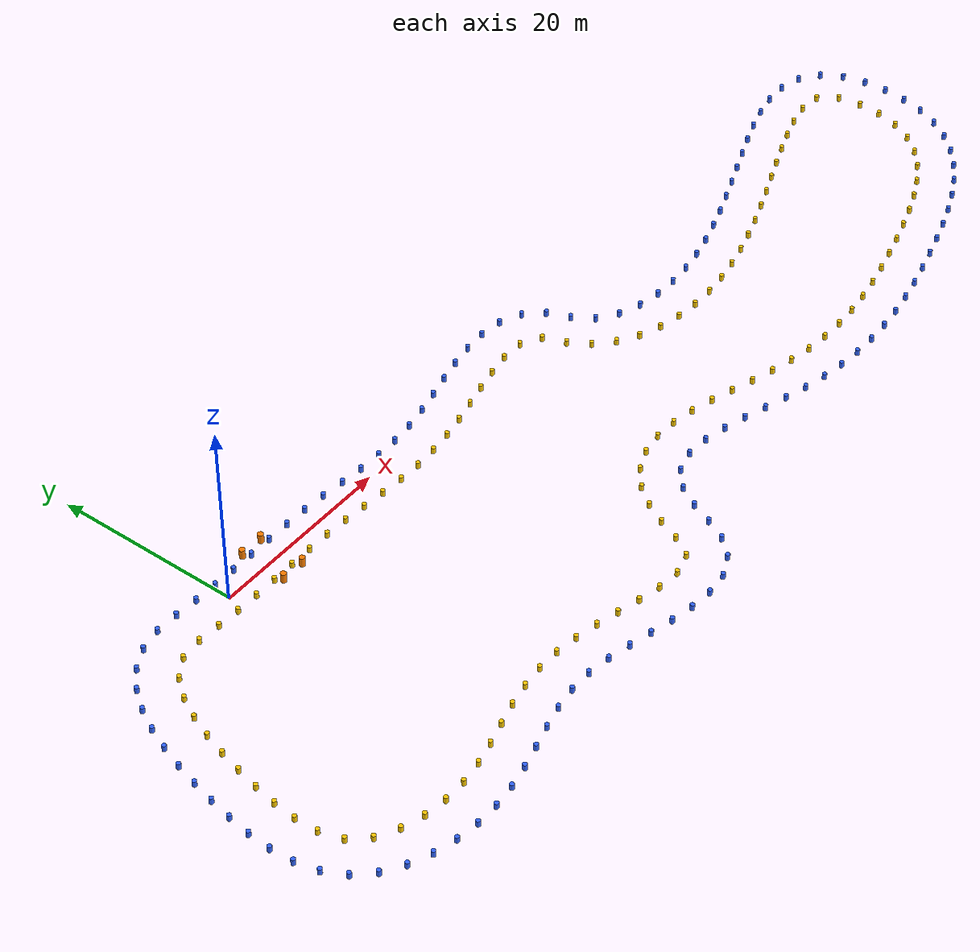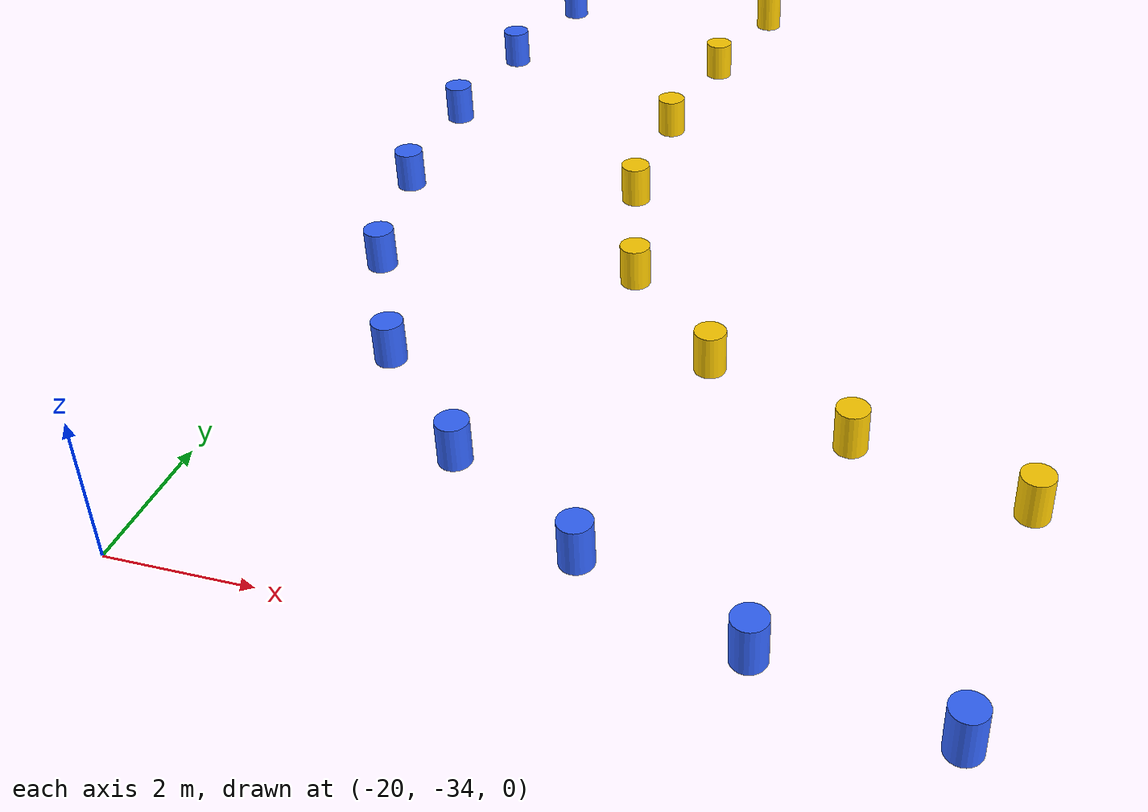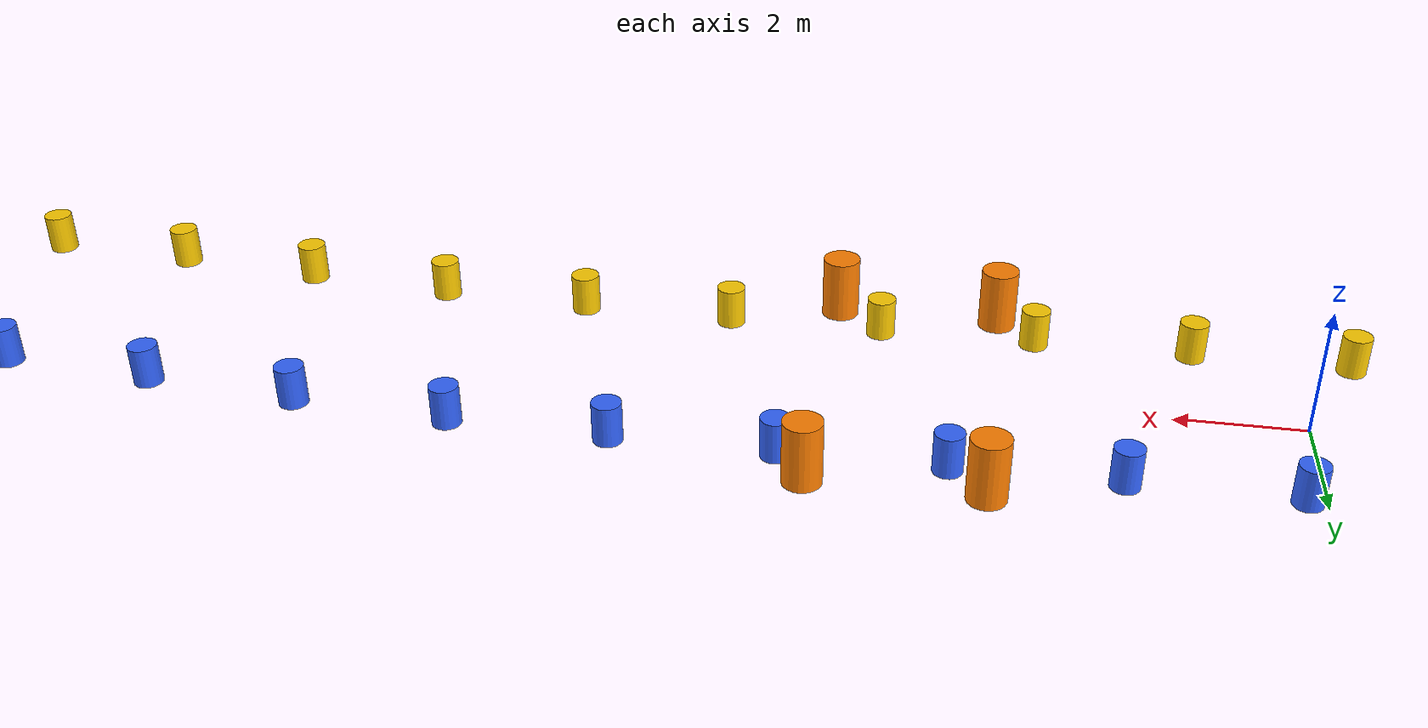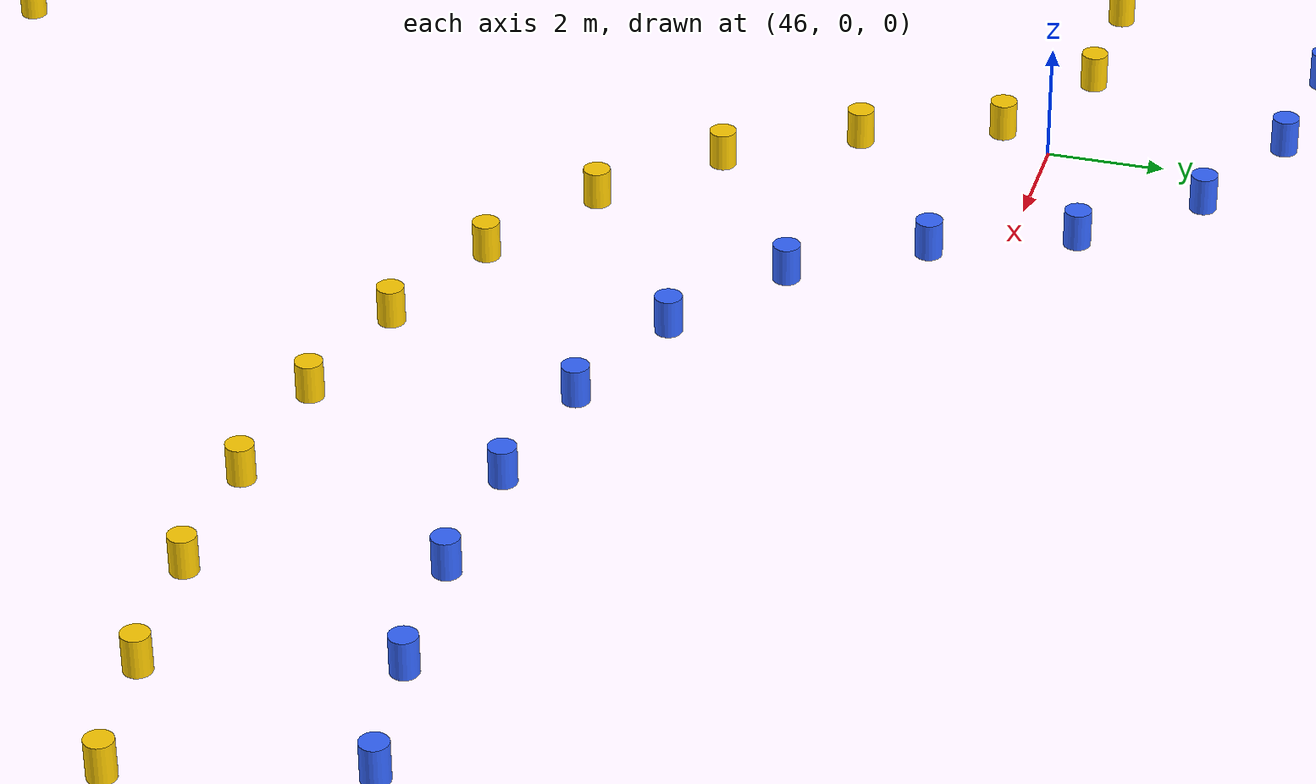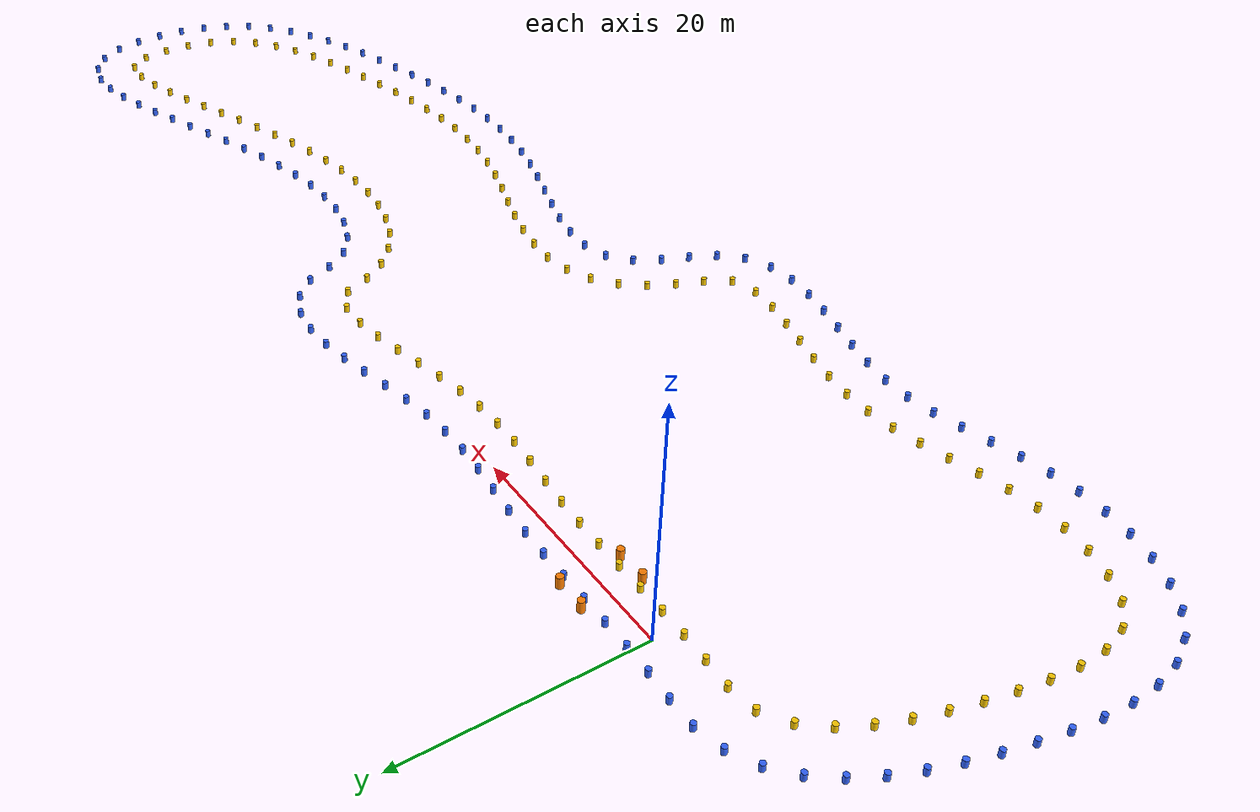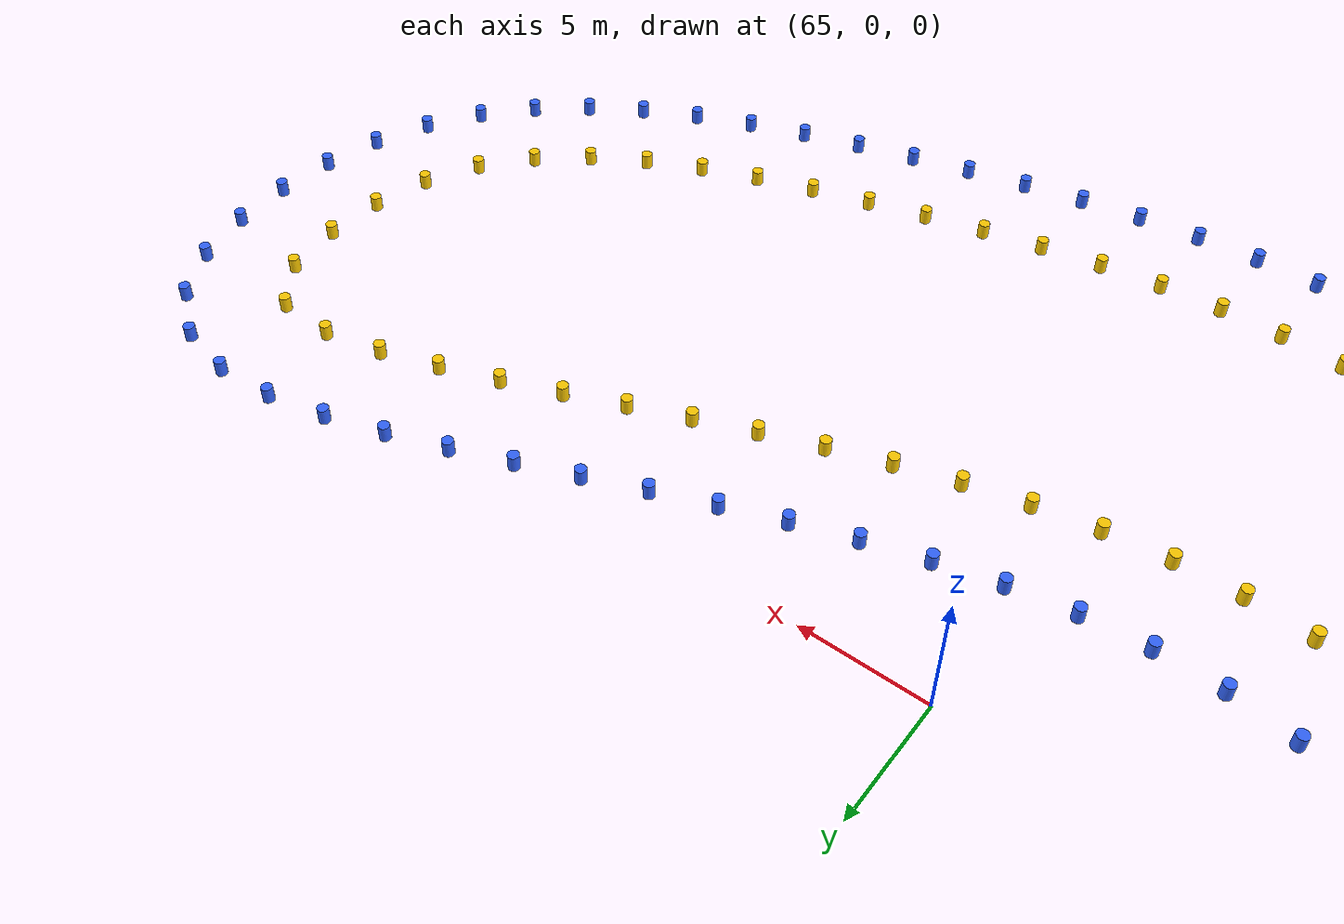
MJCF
<?xml version="1.0" ?>
<mujoco model="random_track">
  <compiler angle="radian" coordinate="local" autolimits="true"/>
  <default>
    <default class="cone">
      <joint type="free" damping="0.1" frictionloss="0.05"/>
      <geom condim="4" friction="0.5 0.005 0.0001" solref="0.02 1.0" solimp="0.99 0.99 0.001"/>
    </default>
  </default>
  <asset>
    <material name="blue_cone" rgba="0.2 0.4 1.0 1.0" specular="0.5" shininess="0.2"/>
    <material name="yellow_cone" rgba="1.0 0.8 0.0 1.0" specular="0.5" shininess="0.2"/>
    <material name="orange_cone" rgba="1.0 0.5 0.0 1.0" specular="0.5" shininess="0.2"/>
  </asset>
  <worldbody>
    <body name="cone_left_0000" pos="12.261095116007493 -31.503541395943046 0.325">
      <joint name="cone_left_joint_0000" type="free" damping="0.1" frictionloss="0.05"/>
      <geom name="cone_left_vis_0000" type="cylinder" size="0.228 0.325" material="blue_cone" mass="1.0" density="100" condim="4" friction="0.5 0.005 0.0001" solref="0.02 1.0" solimp="0.99 0.99 0.001"/>
    </body>
    <body name="cone_left_0001" pos="9.769956982757048 -31.52037595811393 0.325">
      <joint name="cone_left_joint_0001" type="free" damping="0.1" frictionloss="0.05"/>
      <geom name="cone_left_vis_0001" type="cylinder" size="0.228 0.325" material="blue_cone" mass="1.0" density="100" condim="4" friction="0.5 0.005 0.0001" solref="0.02 1.0" solimp="0.99 0.99 0.001"/>
    </body>
    <body name="cone_left_0002" pos="7.302881969261751 -31.872973913557644 0.325">
      <joint name="cone_left_joint_0002" type="free" damping="0.1" frictionloss="0.05"/>
      <geom name="cone_left_vis_0002" type="cylinder" size="0.228 0.325" material="blue_cone" mass="1.0" density="100" condim="4" friction="0.5 0.005 0.0001" solref="0.02 1.0" solimp="0.99 0.99 0.001"/>
    </body>
    <body name="cone_left_0003" pos="4.876832659844204 -32.44742047828662 0.325">
      <joint name="cone_left_joint_0003" type="free" damping="0.1" frictionloss="0.05"/>
      <geom name="cone_left_vis_0003" type="cylinder" size="0.228 0.325" material="blue_cone" mass="1.0" density="100" condim="4" friction="0.5 0.005 0.0001" solref="0.02 1.0" solimp="0.99 0.99 0.001"/>
    </body>
    <body name="cone_left_0004" pos="2.4734703632205317 -33.11200027691288 0.325">
      <joint name="cone_left_joint_0004" type="free" damping="0.1" frictionloss="0.05"/>
      <geom name="cone_left_vis_0004" type="cylinder" size="0.228 0.325" material="blue_cone" mass="1.0" density="100" condim="4" friction="0.5 0.005 0.0001" solref="0.02 1.0" solimp="0.99 0.99 0.001"/>
    </body>
    <body name="cone_left_0005" pos="0.061407820543060154 -33.743752716131496 0.325">
      <joint name="cone_left_joint_0005" type="free" damping="0.1" frictionloss="0.05"/>
      <geom name="cone_left_vis_0005" type="cylinder" size="0.228 0.325" material="blue_cone" mass="1.0" density="100" condim="4" friction="0.5 0.005 0.0001" solref="0.02 1.0" solimp="0.99 0.99 0.001"/>
    </body>
    <body name="cone_left_0006" pos="-2.382775594463844 -34.234335013010195 0.325">
      <joint name="cone_left_joint_0006" type="free" damping="0.1" frictionloss="0.05"/>
      <geom name="cone_left_vis_0006" type="cylinder" size="0.228 0.325" material="blue_cone" mass="1.0" density="100" condim="4" friction="0.5 0.005 0.0001" solref="0.02 1.0" solimp="0.99 0.99 0.001"/>
    </body>
    <body name="cone_left_0007" pos="-4.8614521187894795 -34.495024151080884 0.325">
      <joint name="cone_left_joint_0007" type="free" damping="0.1" frictionloss="0.05"/>
      <geom name="cone_left_vis_0007" type="cylinder" size="0.228 0.325" material="blue_cone" mass="1.0" density="100" condim="4" friction="0.5 0.005 0.0001" solref="0.02 1.0" solimp="0.99 0.99 0.001"/>
    </body>
    <body name="cone_left_0008" pos="-7.35342314175141 -34.47027153940181 0.325">
      <joint name="cone_left_joint_0008" type="free" damping="0.1" frictionloss="0.05"/>
      <geom name="cone_left_vis_0008" type="cylinder" size="0.228 0.325" material="blue_cone" mass="1.0" density="100" condim="4" friction="0.5 0.005 0.0001" solref="0.02 1.0" solimp="0.99 0.99 0.001"/>
    </body>
    <body name="cone_left_0009" pos="-9.8259361931173 -34.15798111328664 0.325">
      <joint name="cone_left_joint_0009" type="free" damping="0.1" frictionloss="0.05"/>
      <geom name="cone_left_vis_0009" type="cylinder" size="0.228 0.325" material="blue_cone" mass="1.0" density="100" condim="4" friction="0.5 0.005 0.0001" solref="0.02 1.0" solimp="0.99 0.99 0.001"/>
    </body>
    <body name="cone_left_0010" pos="-12.242226964223267 -33.54900297050325 0.325">
      <joint name="cone_left_joint_0010" type="free" damping="0.1" frictionloss="0.05"/>
      <geom name="cone_left_vis_0010" type="cylinder" size="0.228 0.325" material="blue_cone" mass="1.0" density="100" condim="4" friction="0.5 0.005 0.0001" solref="0.02 1.0" solimp="0.99 0.99 0.001"/>
    </body>
    <body name="cone_left_0011" pos="-14.54726329325971 -32.60476699346792 0.325">
      <joint name="cone_left_joint_0011" type="free" damping="0.1" frictionloss="0.05"/>
      <geom name="cone_left_vis_0011" type="cylinder" size="0.228 0.325" material="blue_cone" mass="1.0" density="100" condim="4" friction="0.5 0.005 0.0001" solref="0.02 1.0" solimp="0.99 0.99 0.001"/>
    </body>
    <body name="cone_left_0012" pos="-16.64294277680853 -31.261944027048244 0.325">
      <joint name="cone_left_joint_0012" type="free" damping="0.1" frictionloss="0.05"/>
      <geom name="cone_left_vis_0012" type="cylinder" size="0.228 0.325" material="blue_cone" mass="1.0" density="100" condim="4" friction="0.5 0.005 0.0001" solref="0.02 1.0" solimp="0.99 0.99 0.001"/>
    </body>
    <body name="cone_left_0013" pos="-18.356973580264906 -29.46175790534994 0.325">
      <joint name="cone_left_joint_0013" type="free" damping="0.1" frictionloss="0.05"/>
      <geom name="cone_left_vis_0013" type="cylinder" size="0.228 0.325" material="blue_cone" mass="1.0" density="100" condim="4" friction="0.5 0.005 0.0001" solref="0.02 1.0" solimp="0.99 0.99 0.001"/>
    </body>
    <body name="cone_left_0014" pos="-19.507492432374068 -27.258270650421167 0.325">
      <joint name="cone_left_joint_0014" type="free" damping="0.1" frictionloss="0.05"/>
      <geom name="cone_left_vis_0014" type="cylinder" size="0.228 0.325" material="blue_cone" mass="1.0" density="100" condim="4" friction="0.5 0.005 0.0001" solref="0.02 1.0" solimp="0.99 0.99 0.001"/>
    </body>
    <body name="cone_left_0015" pos="-20.092796386730633 -24.839313206706947 0.325">
      <joint name="cone_left_joint_0015" type="free" damping="0.1" frictionloss="0.05"/>
      <geom name="cone_left_vis_0015" type="cylinder" size="0.228 0.325" material="blue_cone" mass="1.0" density="100" condim="4" friction="0.5 0.005 0.0001" solref="0.02 1.0" solimp="0.99 0.99 0.001"/>
    </body>
    <body name="cone_left_0016" pos="-20.235649224360106 -22.35219347544792 0.325">
      <joint name="cone_left_joint_0016" type="free" damping="0.1" frictionloss="0.05"/>
      <geom name="cone_left_vis_0016" type="cylinder" size="0.228 0.325" material="blue_cone" mass="1.0" density="100" condim="4" friction="0.5 0.005 0.0001" solref="0.02 1.0" solimp="0.99 0.99 0.001"/>
    </body>
    <body name="cone_left_0017" pos="-20.073627383361792 -19.864932484247177 0.325">
      <joint name="cone_left_joint_0017" type="free" damping="0.1" frictionloss="0.05"/>
      <geom name="cone_left_vis_0017" type="cylinder" size="0.228 0.325" material="blue_cone" mass="1.0" density="100" condim="4" friction="0.5 0.005 0.0001" solref="0.02 1.0" solimp="0.99 0.99 0.001"/>
    </body>
    <body name="cone_left_0018" pos="-19.713352899998956 -17.397951590760783 0.325">
      <joint name="cone_left_joint_0018" type="free" damping="0.1" frictionloss="0.05"/>
      <geom name="cone_left_vis_0018" type="cylinder" size="0.228 0.325" material="blue_cone" mass="1.0" density="100" condim="4" friction="0.5 0.005 0.0001" solref="0.02 1.0" solimp="0.99 0.99 0.001"/>
    </body>
    <body name="cone_left_0019" pos="-19.22968578991722 -14.951888321969776 0.325">
      <joint name="cone_left_joint_0019" type="free" damping="0.1" frictionloss="0.05"/>
      <geom name="cone_left_vis_0019" type="cylinder" size="0.228 0.325" material="blue_cone" mass="1.0" density="100" condim="4" friction="0.5 0.005 0.0001" solref="0.02 1.0" solimp="0.99 0.99 0.001"/>
    </body>
    <body name="cone_left_0020" pos="-18.666352505288824 -12.5229007156492 0.325">
      <joint name="cone_left_joint_0020" type="free" damping="0.1" frictionloss="0.05"/>
      <geom name="cone_left_vis_0020" type="cylinder" size="0.228 0.325" material="blue_cone" mass="1.0" density="100" condim="4" friction="0.5 0.005 0.0001" solref="0.02 1.0" solimp="0.99 0.99 0.001"/>
    </body>
    <body name="cone_left_0021" pos="-18.008473945547713 -10.11790130677744 0.325">
      <joint name="cone_left_joint_0021" type="free" damping="0.1" frictionloss="0.05"/>
      <geom name="cone_left_vis_0021" type="cylinder" size="0.228 0.325" material="blue_cone" mass="1.0" density="100" condim="4" friction="0.5 0.005 0.0001" solref="0.02 1.0" solimp="0.99 0.99 0.001"/>
    </body>
    <body name="cone_left_0022" pos="-17.22446216959846 -7.751207866506789 0.325">
      <joint name="cone_left_joint_0022" type="free" damping="0.1" frictionloss="0.05"/>
      <geom name="cone_left_vis_0022" type="cylinder" size="0.228 0.325" material="blue_cone" mass="1.0" density="100" condim="4" friction="0.5 0.005 0.0001" solref="0.02 1.0" solimp="0.99 0.99 0.001"/>
    </body>
    <body name="cone_left_0023" pos="-16.272704245989576 -5.447223006296127 0.325">
      <joint name="cone_left_joint_0023" type="free" damping="0.1" frictionloss="0.05"/>
      <geom name="cone_left_vis_0023" type="cylinder" size="0.228 0.325" material="blue_cone" mass="1.0" density="100" condim="4" friction="0.5 0.005 0.0001" solref="0.02 1.0" solimp="0.99 0.99 0.001"/>
    </body>
    <body name="cone_left_0024" pos="-15.09750104590266 -3.249554238916261 0.325">
      <joint name="cone_left_joint_0024" type="free" damping="0.1" frictionloss="0.05"/>
      <geom name="cone_left_vis_0024" type="cylinder" size="0.228 0.325" material="blue_cone" mass="1.0" density="100" condim="4" friction="0.5 0.005 0.0001" solref="0.02 1.0" solimp="0.99 0.99 0.001"/>
    </body>
    <body name="cone_left_0025" pos="-13.62898142456229 -1.2377071231141912 0.325">
      <joint name="cone_left_joint_0025" type="free" damping="0.1" frictionloss="0.05"/>
      <geom name="cone_left_vis_0025" type="cylinder" size="0.228 0.325" material="blue_cone" mass="1.0" density="100" condim="4" friction="0.5 0.005 0.0001" solref="0.02 1.0" solimp="0.99 0.99 0.001"/>
    </body>
    <body name="cone_left_0026" pos="-11.802868957552297 0.4527048003149474 0.325">
      <joint name="cone_left_joint_0026" type="free" damping="0.1" frictionloss="0.05"/>
      <geom name="cone_left_vis_0026" type="cylinder" size="0.228 0.325" material="blue_cone" mass="1.0" density="100" condim="4" friction="0.5 0.005 0.0001" solref="0.02 1.0" solimp="0.99 0.99 0.001"/>
    </body>
    <body name="cone_left_0027" pos="-9.616115761956879 1.6346197048626152 0.325">
      <joint name="cone_left_joint_0027" type="free" damping="0.1" frictionloss="0.05"/>
      <geom name="cone_left_vis_0027" type="cylinder" size="0.228 0.325" material="blue_cone" mass="1.0" density="100" condim="4" friction="0.5 0.005 0.0001" solref="0.02 1.0" solimp="0.99 0.99 0.001"/>
    </body>
    <body name="cone_left_0028" pos="-7.18628013268248 2.156425486520348 0.325">
      <joint name="cone_left_joint_0028" type="free" damping="0.1" frictionloss="0.05"/>
      <geom name="cone_left_vis_0028" type="cylinder" size="0.228 0.325" material="blue_cone" mass="1.0" density="100" condim="4" friction="0.5 0.005 0.0001" solref="0.02 1.0" solimp="0.99 0.99 0.001"/>
    </body>
    <body name="cone_left_0029" pos="-4.694936270793736 2.1285212166671954 0.325">
      <joint name="cone_left_joint_0029" type="free" damping="0.1" frictionloss="0.05"/>
      <geom name="cone_left_vis_0029" type="cylinder" size="0.228 0.325" material="blue_cone" mass="1.0" density="100" condim="4" friction="0.5 0.005 0.0001" solref="0.02 1.0" solimp="0.99 0.99 0.001"/>
    </body>
    <body name="cone_left_0030" pos="-2.206356751880854 1.9720504513004755 0.325">
      <joint name="cone_left_joint_0030" type="free" damping="0.1" frictionloss="0.05"/>
      <geom name="cone_left_vis_0030" type="cylinder" size="0.228 0.325" material="blue_cone" mass="1.0" density="100" condim="4" friction="0.5 0.005 0.0001" solref="0.02 1.0" solimp="0.99 0.99 0.001"/>
    </body>
    <body name="cone_left_0031" pos="0.2859354025021723 1.8951031468284611 0.325">
      <joint name="cone_left_joint_0031" type="free" damping="0.1" frictionloss="0.05"/>
      <geom name="cone_left_vis_0031" type="cylinder" size="0.228 0.325" material="blue_cone" mass="1.0" density="100" condim="4" friction="0.5 0.005 0.0001" solref="0.02 1.0" solimp="0.99 0.99 0.001"/>
    </body>
    <body name="cone_left_0032" pos="2.779415276054575 1.8783801861263356 0.325">
      <joint name="cone_left_joint_0032" type="free" damping="0.1" frictionloss="0.05"/>
      <geom name="cone_left_vis_0032" type="cylinder" size="0.228 0.325" material="blue_cone" mass="1.0" density="100" condim="4" friction="0.5 0.005 0.0001" solref="0.02 1.0" solimp="0.99 0.99 0.001"/>
    </body>
    <body name="cone_left_0033" pos="5.272934944005531 1.89370177806137 0.325">
      <joint name="cone_left_joint_0033" type="free" damping="0.1" frictionloss="0.05"/>
      <geom name="cone_left_vis_0033" type="cylinder" size="0.228 0.325" material="blue_cone" mass="1.0" density="100" condim="4" friction="0.5 0.005 0.0001" solref="0.02 1.0" solimp="0.99 0.99 0.001"/>
    </body>
    <body name="cone_left_0034" pos="7.766436346025156 1.912165355718102 0.325">
      <joint name="cone_left_joint_0034" type="free" damping="0.1" frictionloss="0.05"/>
      <geom name="cone_left_vis_0034" type="cylinder" size="0.228 0.325" material="blue_cone" mass="1.0" density="100" condim="4" friction="0.5 0.005 0.0001" solref="0.02 1.0" solimp="0.99 0.99 0.001"/>
    </body>
    <body name="cone_left_0035" pos="10.259962752912049 1.9036089445932447 0.325">
      <joint name="cone_left_joint_0035" type="free" damping="0.1" frictionloss="0.05"/>
      <geom name="cone_left_vis_0035" type="cylinder" size="0.228 0.325" material="blue_cone" mass="1.0" density="100" condim="4" friction="0.5 0.005 0.0001" solref="0.02 1.0" solimp="0.99 0.99 0.001"/>
    </body>
    <body name="cone_left_0036" pos="12.75252156650718 1.8360028091714895 0.325">
      <joint name="cone_left_joint_0036" type="free" damping="0.1" frictionloss="0.05"/>
      <geom name="cone_left_vis_0036" type="cylinder" size="0.228 0.325" material="blue_cone" mass="1.0" density="100" condim="4" friction="0.5 0.005 0.0001" solref="0.02 1.0" solimp="0.99 0.99 0.001"/>
    </body>
    <body name="cone_left_0037" pos="15.24091643861188 1.6779172624192285 0.325">
      <joint name="cone_left_joint_0037" type="free" damping="0.1" frictionloss="0.05"/>
      <geom name="cone_left_vis_0037" type="cylinder" size="0.228 0.325" material="blue_cone" mass="1.0" density="100" condim="4" friction="0.5 0.005 0.0001" solref="0.02 1.0" solimp="0.99 0.99 0.001"/>
    </body>
    <body name="cone_left_0038" pos="17.724445478262343 1.4545061786893427 0.325">
      <joint name="cone_left_joint_0038" type="free" damping="0.1" frictionloss="0.05"/>
      <geom name="cone_left_vis_0038" type="cylinder" size="0.228 0.325" material="blue_cone" mass="1.0" density="100" condim="4" friction="0.5 0.005 0.0001" solref="0.02 1.0" solimp="0.99 0.99 0.001"/>
    </body>
    <body name="cone_left_0039" pos="20.20921544917336 1.2458552874654316 0.325">
      <joint name="cone_left_joint_0039" type="free" damping="0.1" frictionloss="0.05"/>
      <geom name="cone_left_vis_0039" type="cylinder" size="0.228 0.325" material="blue_cone" mass="1.0" density="100" condim="4" friction="0.5 0.005 0.0001" solref="0.02 1.0" solimp="0.99 0.99 0.001"/>
    </body>
    <body name="cone_left_0040" pos="22.699938919088854 1.1332199507497478 0.325">
      <joint name="cone_left_joint_0040" type="free" damping="0.1" frictionloss="0.05"/>
      <geom name="cone_left_vis_0040" type="cylinder" size="0.228 0.325" material="blue_cone" mass="1.0" density="100" condim="4" friction="0.5 0.005 0.0001" solref="0.02 1.0" solimp="0.99 0.99 0.001"/>
    </body>
    <body name="cone_left_0041" pos="25.19243735575402 1.1823058324201696 0.325">
      <joint name="cone_left_joint_0041" type="free" damping="0.1" frictionloss="0.05"/>
      <geom name="cone_left_vis_0041" type="cylinder" size="0.228 0.325" material="blue_cone" mass="1.0" density="100" condim="4" friction="0.5 0.005 0.0001" solref="0.02 1.0" solimp="0.99 0.99 0.001"/>
    </body>
    <body name="cone_left_0042" pos="27.672889918339212 1.430385095243409 0.325">
      <joint name="cone_left_joint_0042" type="free" damping="0.1" frictionloss="0.05"/>
      <geom name="cone_left_vis_0042" type="cylinder" size="0.228 0.325" material="blue_cone" mass="1.0" density="100" condim="4" friction="0.5 0.005 0.0001" solref="0.02 1.0" solimp="0.99 0.99 0.001"/>
    </body>
    <body name="cone_left_0043" pos="30.126006166327638 1.8749368471860777 0.325">
      <joint name="cone_left_joint_0043" type="free" damping="0.1" frictionloss="0.05"/>
      <geom name="cone_left_vis_0043" type="cylinder" size="0.228 0.325" material="blue_cone" mass="1.0" density="100" condim="4" friction="0.5 0.005 0.0001" solref="0.02 1.0" solimp="0.99 0.99 0.001"/>
    </body>
    <body name="cone_left_0044" pos="32.5565301471993 2.4317835209036076 0.325">
      <joint name="cone_left_joint_0044" type="free" damping="0.1" frictionloss="0.05"/>
      <geom name="cone_left_vis_0044" type="cylinder" size="0.228 0.325" material="blue_cone" mass="1.0" density="100" condim="4" friction="0.5 0.005 0.0001" solref="0.02 1.0" solimp="0.99 0.99 0.001"/>
    </body>
    <body name="cone_left_0045" pos="34.98078536683602 3.01562968895567 0.325">
      <joint name="cone_left_joint_0045" type="free" damping="0.1" frictionloss="0.05"/>
      <geom name="cone_left_vis_0045" type="cylinder" size="0.228 0.325" material="blue_cone" mass="1.0" density="100" condim="4" friction="0.5 0.005 0.0001" solref="0.02 1.0" solimp="0.99 0.99 0.001"/>
    </body>
    <body name="cone_left_0046" pos="37.41488241674965 3.556464501821054 0.325">
      <joint name="cone_left_joint_0046" type="free" damping="0.1" frictionloss="0.05"/>
      <geom name="cone_left_vis_0046" type="cylinder" size="0.228 0.325" material="blue_cone" mass="1.0" density="100" condim="4" friction="0.5 0.005 0.0001" solref="0.02 1.0" solimp="0.99 0.99 0.001"/>
    </body>
    <body name="cone_left_0047" pos="39.87274526553581 3.9737920987463298 0.325">
      <joint name="cone_left_joint_0047" type="free" damping="0.1" frictionloss="0.05"/>
      <geom name="cone_left_vis_0047" type="cylinder" size="0.228 0.325" material="blue_cone" mass="1.0" density="100" condim="4" friction="0.5 0.005 0.0001" solref="0.02 1.0" solimp="0.99 0.99 0.001"/>
    </body>
    <body name="cone_left_0048" pos="42.35853973733094 4.145355483726561 0.325">
      <joint name="cone_left_joint_0048" type="free" damping="0.1" frictionloss="0.05"/>
      <geom name="cone_left_vis_0048" type="cylinder" size="0.228 0.325" material="blue_cone" mass="1.0" density="100" condim="4" friction="0.5 0.005 0.0001" solref="0.02 1.0" solimp="0.99 0.99 0.001"/>
    </body>
    <body name="cone_left_0049" pos="44.83073496894367 3.868486663938569 0.325">
      <joint name="cone_left_joint_0049" type="free" damping="0.1" frictionloss="0.05"/>
      <geom name="cone_left_vis_0049" type="cylinder" size="0.228 0.325" material="blue_cone" mass="1.0" density="100" condim="4" friction="0.5 0.005 0.0001" solref="0.02 1.0" solimp="0.99 0.99 0.001"/>
    </body>
    <body name="cone_left_0050" pos="47.1011331881427 2.8722603905161748 0.325">
      <joint name="cone_left_joint_0050" type="free" damping="0.1" frictionloss="0.05"/>
      <geom name="cone_left_vis_0050" type="cylinder" size="0.228 0.325" material="blue_cone" mass="1.0" density="100" condim="4" friction="0.5 0.005 0.0001" solref="0.02 1.0" solimp="0.99 0.99 0.001"/>
    </body>
    <body name="cone_left_0051" pos="48.79433183721524 1.0669954292702926 0.325">
      <joint name="cone_left_joint_0051" type="free" damping="0.1" frictionloss="0.05"/>
      <geom name="cone_left_vis_0051" type="cylinder" size="0.228 0.325" material="blue_cone" mass="1.0" density="100" condim="4" friction="0.5 0.005 0.0001" solref="0.02 1.0" solimp="0.99 0.99 0.001"/>
    </body>
    <body name="cone_left_0052" pos="49.75132459158125 -1.2291283030840532 0.325">
      <joint name="cone_left_joint_0052" type="free" damping="0.1" frictionloss="0.05"/>
      <geom name="cone_left_vis_0052" type="cylinder" size="0.228 0.325" material="blue_cone" mass="1.0" density="100" condim="4" friction="0.5 0.005 0.0001" solref="0.02 1.0" solimp="0.99 0.99 0.001"/>
    </body>
    <body name="cone_left_0053" pos="51.116868478447174 -3.2933618444744894 0.325">
      <joint name="cone_left_joint_0053" type="free" damping="0.1" frictionloss="0.05"/>
      <geom name="cone_left_vis_0053" type="cylinder" size="0.228 0.325" material="blue_cone" mass="1.0" density="100" condim="4" friction="0.5 0.005 0.0001" solref="0.02 1.0" solimp="0.99 0.99 0.001"/>
    </body>
    <body name="cone_left_0054" pos="53.15539255141243 -4.710430651660943 0.325">
      <joint name="cone_left_joint_0054" type="free" damping="0.1" frictionloss="0.05"/>
      <geom name="cone_left_vis_0054" type="cylinder" size="0.228 0.325" material="blue_cone" mass="1.0" density="100" condim="4" friction="0.5 0.005 0.0001" solref="0.02 1.0" solimp="0.99 0.99 0.001"/>
    </body>
    <body name="cone_left_0055" pos="55.499481195484705 -5.546817881779134 0.325">
      <joint name="cone_left_joint_0055" type="free" damping="0.1" frictionloss="0.05"/>
      <geom name="cone_left_vis_0055" type="cylinder" size="0.228 0.325" material="blue_cone" mass="1.0" density="100" condim="4" friction="0.5 0.005 0.0001" solref="0.02 1.0" solimp="0.99 0.99 0.001"/>
    </body>
    <body name="cone_left_0056" pos="57.9577017551928 -5.950739935004677 0.325">
      <joint name="cone_left_joint_0056" type="free" damping="0.1" frictionloss="0.05"/>
      <geom name="cone_left_vis_0056" type="cylinder" size="0.228 0.325" material="blue_cone" mass="1.0" density="100" condim="4" friction="0.5 0.005 0.0001" solref="0.02 1.0" solimp="0.99 0.99 0.001"/>
    </body>
    <body name="cone_left_0057" pos="60.44873367304021 -6.023857622288688 0.325">
      <joint name="cone_left_joint_0057" type="free" damping="0.1" frictionloss="0.05"/>
      <geom name="cone_left_vis_0057" type="cylinder" size="0.228 0.325" material="blue_cone" mass="1.0" density="100" condim="4" friction="0.5 0.005 0.0001" solref="0.02 1.0" solimp="0.99 0.99 0.001"/>
    </body>
    <body name="cone_left_0058" pos="62.933451705097596 -5.826706947941801 0.325">
      <joint name="cone_left_joint_0058" type="free" damping="0.1" frictionloss="0.05"/>
      <geom name="cone_left_vis_0058" type="cylinder" size="0.228 0.325" material="blue_cone" mass="1.0" density="100" condim="4" friction="0.5 0.005 0.0001" solref="0.02 1.0" solimp="0.99 0.99 0.001"/>
    </body>
    <body name="cone_left_0059" pos="65.39080295080939 -5.4071024131401515 0.325">
      <joint name="cone_left_joint_0059" type="free" damping="0.1" frictionloss="0.05"/>
      <geom name="cone_left_vis_0059" type="cylinder" size="0.228 0.325" material="blue_cone" mass="1.0" density="100" condim="4" friction="0.5 0.005 0.0001" solref="0.02 1.0" solimp="0.99 0.99 0.001"/>
    </body>
    <body name="cone_left_0060" pos="67.81356383027719 -4.818707192428718 0.325">
      <joint name="cone_left_joint_0060" type="free" damping="0.1" frictionloss="0.05"/>
      <geom name="cone_left_vis_0060" type="cylinder" size="0.228 0.325" material="blue_cone" mass="1.0" density="100" condim="4" friction="0.5 0.005 0.0001" solref="0.02 1.0" solimp="0.99 0.99 0.001"/>
    </body>
    <body name="cone_left_0061" pos="70.20185826065378 -4.102562047079445 0.325">
      <joint name="cone_left_joint_0061" type="free" damping="0.1" frictionloss="0.05"/>
      <geom name="cone_left_vis_0061" type="cylinder" size="0.228 0.325" material="blue_cone" mass="1.0" density="100" condim="4" friction="0.5 0.005 0.0001" solref="0.02 1.0" solimp="0.99 0.99 0.001"/>
    </body>
    <body name="cone_left_0062" pos="72.55978662369138 -3.2917155504534463 0.325">
      <joint name="cone_left_joint_0062" type="free" damping="0.1" frictionloss="0.05"/>
      <geom name="cone_left_vis_0062" type="cylinder" size="0.228 0.325" material="blue_cone" mass="1.0" density="100" condim="4" friction="0.5 0.005 0.0001" solref="0.02 1.0" solimp="0.99 0.99 0.001"/>
    </body>
    <body name="cone_left_0063" pos="74.89325007097281 -2.4127667836689426 0.325">
      <joint name="cone_left_joint_0063" type="free" damping="0.1" frictionloss="0.05"/>
      <geom name="cone_left_vis_0063" type="cylinder" size="0.228 0.325" material="blue_cone" mass="1.0" density="100" condim="4" friction="0.5 0.005 0.0001" solref="0.02 1.0" solimp="0.99 0.99 0.001"/>
    </body>
    <body name="cone_left_0064" pos="77.20926075113991 -1.4887080424516768 0.325">
      <joint name="cone_left_joint_0064" type="free" damping="0.1" frictionloss="0.05"/>
      <geom name="cone_left_vis_0064" type="cylinder" size="0.228 0.325" material="blue_cone" mass="1.0" density="100" condim="4" friction="0.5 0.005 0.0001" solref="0.02 1.0" solimp="0.99 0.99 0.001"/>
    </body>
    <body name="cone_left_0065" pos="79.51583009462902 -0.5412771464907706 0.325">
      <joint name="cone_left_joint_0065" type="free" damping="0.1" frictionloss="0.05"/>
      <geom name="cone_left_vis_0065" type="cylinder" size="0.228 0.325" material="blue_cone" mass="1.0" density="100" condim="4" friction="0.5 0.005 0.0001" solref="0.02 1.0" solimp="0.99 0.99 0.001"/>
    </body>
    <body name="cone_left_0066" pos="81.82219115906483 0.4066607085945293 0.325">
      <joint name="cone_left_joint_0066" type="free" damping="0.1" frictionloss="0.05"/>
      <geom name="cone_left_vis_0066" type="cylinder" size="0.228 0.325" material="blue_cone" mass="1.0" density="100" condim="4" friction="0.5 0.005 0.0001" solref="0.02 1.0" solimp="0.99 0.99 0.001"/>
    </body>
    <body name="cone_left_0067" pos="84.13922568497365 1.3281147585494608 0.325">
      <joint name="cone_left_joint_0067" type="free" damping="0.1" frictionloss="0.05"/>
      <geom name="cone_left_vis_0067" type="cylinder" size="0.228 0.325" material="blue_cone" mass="1.0" density="100" condim="4" friction="0.5 0.005 0.0001" solref="0.02 1.0" solimp="0.99 0.99 0.001"/>
    </body>
    <body name="cone_left_0068" pos="86.48039012100239 2.1861004865256746 0.325">
      <joint name="cone_left_joint_0068" type="free" damping="0.1" frictionloss="0.05"/>
      <geom name="cone_left_vis_0068" type="cylinder" size="0.228 0.325" material="blue_cone" mass="1.0" density="100" condim="4" friction="0.5 0.005 0.0001" solref="0.02 1.0" solimp="0.99 0.99 0.001"/>
    </body>
    <body name="cone_left_0069" pos="88.86183105963448 2.9238645007742576 0.325">
      <joint name="cone_left_joint_0069" type="free" damping="0.1" frictionloss="0.05"/>
      <geom name="cone_left_vis_0069" type="cylinder" size="0.228 0.325" material="blue_cone" mass="1.0" density="100" condim="4" friction="0.5 0.005 0.0001" solref="0.02 1.0" solimp="0.99 0.99 0.001"/>
    </body>
    <body name="cone_left_0070" pos="91.29917916695723 3.4432791551563895 0.325">
      <joint name="cone_left_joint_0070" type="free" damping="0.1" frictionloss="0.05"/>
      <geom name="cone_left_vis_0070" type="cylinder" size="0.228 0.325" material="blue_cone" mass="1.0" density="100" condim="4" friction="0.5 0.005 0.0001" solref="0.02 1.0" solimp="0.99 0.99 0.001"/>
    </body>
    <body name="cone_left_0071" pos="93.78511603927828 3.563787773001465 0.325">
      <joint name="cone_left_joint_0071" type="free" damping="0.1" frictionloss="0.05"/>
      <geom name="cone_left_vis_0071" type="cylinder" size="0.228 0.325" material="blue_cone" mass="1.0" density="100" condim="4" friction="0.5 0.005 0.0001" solref="0.02 1.0" solimp="0.99 0.99 0.001"/>
    </body>
    <body name="cone_left_0072" pos="96.20076224912272 2.9979426214716227 0.325">
      <joint name="cone_left_joint_0072" type="free" damping="0.1" frictionloss="0.05"/>
      <geom name="cone_left_vis_0072" type="cylinder" size="0.228 0.325" material="blue_cone" mass="1.0" density="100" condim="4" friction="0.5 0.005 0.0001" solref="0.02 1.0" solimp="0.99 0.99 0.001"/>
    </body>
    <body name="cone_left_0073" pos="98.20394987893111 1.5453814257545702 0.325">
      <joint name="cone_left_joint_0073" type="free" damping="0.1" frictionloss="0.05"/>
      <geom name="cone_left_vis_0073" type="cylinder" size="0.228 0.325" material="blue_cone" mass="1.0" density="100" condim="4" friction="0.5 0.005 0.0001" solref="0.02 1.0" solimp="0.99 0.99 0.001"/>
    </body>
    <body name="cone_left_0074" pos="99.47578229615857 -0.5835715924062015 0.325">
      <joint name="cone_left_joint_0074" type="free" damping="0.1" frictionloss="0.05"/>
      <geom name="cone_left_vis_0074" type="cylinder" size="0.228 0.325" material="blue_cone" mass="1.0" density="100" condim="4" friction="0.5 0.005 0.0001" solref="0.02 1.0" solimp="0.99 0.99 0.001"/>
    </body>
    <body name="cone_left_0075" pos="100.0786078000699 -2.9977481831303976 0.325">
      <joint name="cone_left_joint_0075" type="free" damping="0.1" frictionloss="0.05"/>
      <geom name="cone_left_vis_0075" type="cylinder" size="0.228 0.325" material="blue_cone" mass="1.0" density="100" condim="4" friction="0.5 0.005 0.0001" solref="0.02 1.0" solimp="0.99 0.99 0.001"/>
    </body>
    <body name="cone_left_0076" pos="100.2345410459849 -5.483986241018442 0.325">
      <joint name="cone_left_joint_0076" type="free" damping="0.1" frictionloss="0.05"/>
      <geom name="cone_left_vis_0076" type="cylinder" size="0.228 0.325" material="blue_cone" mass="1.0" density="100" condim="4" friction="0.5 0.005 0.0001" solref="0.02 1.0" solimp="0.99 0.99 0.001"/>
    </body>
    <body name="cone_left_0077" pos="100.03937225622782 -7.967975286039959 0.325">
      <joint name="cone_left_joint_0077" type="free" damping="0.1" frictionloss="0.05"/>
      <geom name="cone_left_vis_0077" type="cylinder" size="0.228 0.325" material="blue_cone" mass="1.0" density="100" condim="4" friction="0.5 0.005 0.0001" solref="0.02 1.0" solimp="0.99 0.99 0.001"/>
    </body>
    <body name="cone_left_0078" pos="99.49369566300464 -10.39862059931535 0.325">
      <joint name="cone_left_joint_0078" type="free" damping="0.1" frictionloss="0.05"/>
      <geom name="cone_left_vis_0078" type="cylinder" size="0.228 0.325" material="blue_cone" mass="1.0" density="100" condim="4" friction="0.5 0.005 0.0001" solref="0.02 1.0" solimp="0.99 0.99 0.001"/>
    </body>
    <body name="cone_left_0079" pos="98.55242972115467 -12.704097482397387 0.325">
      <joint name="cone_left_joint_0079" type="free" damping="0.1" frictionloss="0.05"/>
      <geom name="cone_left_vis_0079" type="cylinder" size="0.228 0.325" material="blue_cone" mass="1.0" density="100" condim="4" friction="0.5 0.005 0.0001" solref="0.02 1.0" solimp="0.99 0.99 0.001"/>
    </body>
    <body name="cone_left_0080" pos="97.21905885060347 -14.807441341277595 0.325">
      <joint name="cone_left_joint_0080" type="free" damping="0.1" frictionloss="0.05"/>
      <geom name="cone_left_vis_0080" type="cylinder" size="0.228 0.325" material="blue_cone" mass="1.0" density="100" condim="4" friction="0.5 0.005 0.0001" solref="0.02 1.0" solimp="0.99 0.99 0.001"/>
    </body>
    <body name="cone_left_0081" pos="95.5542862046806 -16.660379307392432 0.325">
      <joint name="cone_left_joint_0081" type="free" damping="0.1" frictionloss="0.05"/>
      <geom name="cone_left_vis_0081" type="cylinder" size="0.228 0.325" material="blue_cone" mass="1.0" density="100" condim="4" friction="0.5 0.005 0.0001" solref="0.02 1.0" solimp="0.99 0.99 0.001"/>
    </body>
    <body name="cone_left_0082" pos="93.63794526263489 -18.25291972410936 0.325">
      <joint name="cone_left_joint_0082" type="free" damping="0.1" frictionloss="0.05"/>
      <geom name="cone_left_vis_0082" type="cylinder" size="0.228 0.325" material="blue_cone" mass="1.0" density="100" condim="4" friction="0.5 0.005 0.0001" solref="0.02 1.0" solimp="0.99 0.99 0.001"/>
    </body>
    <body name="cone_left_0083" pos="91.54444646556394 -19.60535837420312 0.325">
      <joint name="cone_left_joint_0083" type="free" damping="0.1" frictionloss="0.05"/>
      <geom name="cone_left_vis_0083" type="cylinder" size="0.228 0.325" material="blue_cone" mass="1.0" density="100" condim="4" friction="0.5 0.005 0.0001" solref="0.02 1.0" solimp="0.99 0.99 0.001"/>
    </body>
    <body name="cone_left_0084" pos="89.33151974065922 -20.753033320946926 0.325">
      <joint name="cone_left_joint_0084" type="free" damping="0.1" frictionloss="0.05"/>
      <geom name="cone_left_vis_0084" type="cylinder" size="0.228 0.325" material="blue_cone" mass="1.0" density="100" condim="4" friction="0.5 0.005 0.0001" solref="0.02 1.0" solimp="0.99 0.99 0.001"/>
    </body>
    <body name="cone_left_0085" pos="87.03981634640313 -21.73479027405523 0.325">
      <joint name="cone_left_joint_0085" type="free" damping="0.1" frictionloss="0.05"/>
      <geom name="cone_left_vis_0085" type="cylinder" size="0.228 0.325" material="blue_cone" mass="1.0" density="100" condim="4" friction="0.5 0.005 0.0001" solref="0.02 1.0" solimp="0.99 0.99 0.001"/>
    </body>
    <body name="cone_left_0086" pos="84.6968367496158 -22.58753419576962 0.325">
      <joint name="cone_left_joint_0086" type="free" damping="0.1" frictionloss="0.05"/>
      <geom name="cone_left_vis_0086" type="cylinder" size="0.228 0.325" material="blue_cone" mass="1.0" density="100" condim="4" friction="0.5 0.005 0.0001" solref="0.02 1.0" solimp="0.99 0.99 0.001"/>
    </body>
    <body name="cone_left_0087" pos="82.3212039651945 -23.34496256845395 0.325">
      <joint name="cone_left_joint_0087" type="free" damping="0.1" frictionloss="0.05"/>
      <geom name="cone_left_vis_0087" type="cylinder" size="0.228 0.325" material="blue_cone" mass="1.0" density="100" condim="4" friction="0.5 0.005 0.0001" solref="0.02 1.0" solimp="0.99 0.99 0.001"/>
    </body>
    <body name="cone_left_0088" pos="79.92625516828754 -24.03916476600942 0.325">
      <joint name="cone_left_joint_0088" type="free" damping="0.1" frictionloss="0.05"/>
      <geom name="cone_left_vis_0088" type="cylinder" size="0.228 0.325" material="blue_cone" mass="1.0" density="100" condim="4" friction="0.5 0.005 0.0001" solref="0.02 1.0" solimp="0.99 0.99 0.001"/>
    </body>
    <body name="cone_left_0089" pos="77.5191191911325 -24.689850739999002 0.325">
      <joint name="cone_left_joint_0089" type="free" damping="0.1" frictionloss="0.05"/>
      <geom name="cone_left_vis_0089" type="cylinder" size="0.228 0.325" material="blue_cone" mass="1.0" density="100" condim="4" friction="0.5 0.005 0.0001" solref="0.02 1.0" solimp="0.99 0.99 0.001"/>
    </body>
    <body name="cone_left_0090" pos="75.09696602238397 -25.282008033491408 0.325">
      <joint name="cone_left_joint_0090" type="free" damping="0.1" frictionloss="0.05"/>
      <geom name="cone_left_vis_0090" type="cylinder" size="0.228 0.325" material="blue_cone" mass="1.0" density="100" condim="4" friction="0.5 0.005 0.0001" solref="0.02 1.0" solimp="0.99 0.99 0.001"/>
    </body>
    <body name="cone_left_0091" pos="72.65654403473965 -25.79336854875835 0.325">
      <joint name="cone_left_joint_0091" type="free" damping="0.1" frictionloss="0.05"/>
      <geom name="cone_left_vis_0091" type="cylinder" size="0.228 0.325" material="blue_cone" mass="1.0" density="100" condim="4" friction="0.5 0.005 0.0001" solref="0.02 1.0" solimp="0.99 0.99 0.001"/>
    </body>
    <body name="cone_left_0092" pos="70.19670175419691 -26.200685511476493 0.325">
      <joint name="cone_left_joint_0092" type="free" damping="0.1" frictionloss="0.05"/>
      <geom name="cone_left_vis_0092" type="cylinder" size="0.228 0.325" material="blue_cone" mass="1.0" density="100" condim="4" friction="0.5 0.005 0.0001" solref="0.02 1.0" solimp="0.99 0.99 0.001"/>
    </body>
    <body name="cone_left_0093" pos="67.7192864717048 -26.481186947166606 0.325">
      <joint name="cone_left_joint_0093" type="free" damping="0.1" frictionloss="0.05"/>
      <geom name="cone_left_vis_0093" type="cylinder" size="0.228 0.325" material="blue_cone" mass="1.0" density="100" condim="4" friction="0.5 0.005 0.0001" solref="0.02 1.0" solimp="0.99 0.99 0.001"/>
    </body>
    <body name="cone_left_0094" pos="65.22970845575736 -26.61472018064184 0.325">
      <joint name="cone_left_joint_0094" type="free" damping="0.1" frictionloss="0.05"/>
      <geom name="cone_left_vis_0094" type="cylinder" size="0.228 0.325" material="blue_cone" mass="1.0" density="100" condim="4" friction="0.5 0.005 0.0001" solref="0.02 1.0" solimp="0.99 0.99 0.001"/>
    </body>
    <body name="cone_left_0095" pos="62.73677868337275 -26.586057971278393 0.325">
      <joint name="cone_left_joint_0095" type="free" damping="0.1" frictionloss="0.05"/>
      <geom name="cone_left_vis_0095" type="cylinder" size="0.228 0.325" material="blue_cone" mass="1.0" density="100" condim="4" friction="0.5 0.005 0.0001" solref="0.02 1.0" solimp="0.99 0.99 0.001"/>
    </body>
    <body name="cone_left_0096" pos="60.25173303548188 -26.38625770110228 0.325">
      <joint name="cone_left_joint_0096" type="free" damping="0.1" frictionloss="0.05"/>
      <geom name="cone_left_vis_0096" type="cylinder" size="0.228 0.325" material="blue_cone" mass="1.0" density="100" condim="4" friction="0.5 0.005 0.0001" solref="0.02 1.0" solimp="0.99 0.99 0.001"/>
    </body>
    <body name="cone_left_0097" pos="57.78653341258055 -26.01450947219361 0.325">
      <joint name="cone_left_joint_0097" type="free" damping="0.1" frictionloss="0.05"/>
      <geom name="cone_left_vis_0097" type="cylinder" size="0.228 0.325" material="blue_cone" mass="1.0" density="100" condim="4" friction="0.5 0.005 0.0001" solref="0.02 1.0" solimp="0.99 0.99 0.001"/>
    </body>
    <body name="cone_left_0098" pos="55.35223208350189 -25.476191755967776 0.325">
      <joint name="cone_left_joint_0098" type="free" damping="0.1" frictionloss="0.05"/>
      <geom name="cone_left_vis_0098" type="cylinder" size="0.228 0.325" material="blue_cone" mass="1.0" density="100" condim="4" friction="0.5 0.005 0.0001" solref="0.02 1.0" solimp="0.99 0.99 0.001"/>
    </body>
    <body name="cone_left_0099" pos="52.95289595249149 -24.79793327170735 0.325">
      <joint name="cone_left_joint_0099" type="free" damping="0.1" frictionloss="0.05"/>
      <geom name="cone_left_vis_0099" type="cylinder" size="0.228 0.325" material="blue_cone" mass="1.0" density="100" condim="4" friction="0.5 0.005 0.0001" solref="0.02 1.0" solimp="0.99 0.99 0.001"/>
    </body>
    <body name="cone_left_0100" pos="50.57434550135001 -24.049411483914923 0.325">
      <joint name="cone_left_joint_0100" type="free" damping="0.1" frictionloss="0.05"/>
      <geom name="cone_left_vis_0100" type="cylinder" size="0.228 0.325" material="blue_cone" mass="1.0" density="100" condim="4" friction="0.5 0.005 0.0001" solref="0.02 1.0" solimp="0.99 0.99 0.001"/>
    </body>
    <body name="cone_left_0101" pos="48.195779792846 -23.30094382336975 0.325">
      <joint name="cone_left_joint_0101" type="free" damping="0.1" frictionloss="0.05"/>
      <geom name="cone_left_vis_0101" type="cylinder" size="0.228 0.325" material="blue_cone" mass="1.0" density="100" condim="4" friction="0.5 0.005 0.0001" solref="0.02 1.0" solimp="0.99 0.99 0.001"/>
    </body>
    <body name="cone_left_0102" pos="45.7947784600547 -22.628827306141744 0.325">
      <joint name="cone_left_joint_0102" type="free" damping="0.1" frictionloss="0.05"/>
      <geom name="cone_left_vis_0102" type="cylinder" size="0.228 0.325" material="blue_cone" mass="1.0" density="100" condim="4" friction="0.5 0.005 0.0001" solref="0.02 1.0" solimp="0.99 0.99 0.001"/>
    </body>
    <body name="cone_left_0103" pos="43.35053016868915 -22.14133000396123 0.325">
      <joint name="cone_left_joint_0103" type="free" damping="0.1" frictionloss="0.05"/>
      <geom name="cone_left_vis_0103" type="cylinder" size="0.228 0.325" material="blue_cone" mass="1.0" density="100" condim="4" friction="0.5 0.005 0.0001" solref="0.02 1.0" solimp="0.99 0.99 0.001"/>
    </body>
    <body name="cone_left_0104" pos="40.86399078611693 -22.034626641018335 0.325">
      <joint name="cone_left_joint_0104" type="free" damping="0.1" frictionloss="0.05"/>
      <geom name="cone_left_vis_0104" type="cylinder" size="0.228 0.325" material="blue_cone" mass="1.0" density="100" condim="4" friction="0.5 0.005 0.0001" solref="0.02 1.0" solimp="0.99 0.99 0.001"/>
    </body>
    <body name="cone_left_0105" pos="38.47583378805241 -22.686067304941773 0.325">
      <joint name="cone_left_joint_0105" type="free" damping="0.1" frictionloss="0.05"/>
      <geom name="cone_left_vis_0105" type="cylinder" size="0.228 0.325" material="blue_cone" mass="1.0" density="100" condim="4" friction="0.5 0.005 0.0001" solref="0.02 1.0" solimp="0.99 0.99 0.001"/>
    </body>
    <body name="cone_left_0106" pos="36.61761385457048 -24.32039671199557 0.325">
      <joint name="cone_left_joint_0106" type="free" damping="0.1" frictionloss="0.05"/>
      <geom name="cone_left_vis_0106" type="cylinder" size="0.228 0.325" material="blue_cone" mass="1.0" density="100" condim="4" friction="0.5 0.005 0.0001" solref="0.02 1.0" solimp="0.99 0.99 0.001"/>
    </body>
    <body name="cone_left_0107" pos="35.375333020518326 -26.475327640862147 0.325">
      <joint name="cone_left_joint_0107" type="free" damping="0.1" frictionloss="0.05"/>
      <geom name="cone_left_vis_0107" type="cylinder" size="0.228 0.325" material="blue_cone" mass="1.0" density="100" condim="4" friction="0.5 0.005 0.0001" solref="0.02 1.0" solimp="0.99 0.99 0.001"/>
    </body>
    <body name="cone_left_0108" pos="34.42418046234383 -28.780224177925263 0.325">
      <joint name="cone_left_joint_0108" type="free" damping="0.1" frictionloss="0.05"/>
      <geom name="cone_left_vis_0108" type="cylinder" size="0.228 0.325" material="blue_cone" mass="1.0" density="100" condim="4" friction="0.5 0.005 0.0001" solref="0.02 1.0" solimp="0.99 0.99 0.001"/>
    </body>
    <body name="cone_left_0109" pos="33.322042767102204 -31.01372286031193 0.325">
      <joint name="cone_left_joint_0109" type="free" damping="0.1" frictionloss="0.05"/>
      <geom name="cone_left_vis_0109" type="cylinder" size="0.228 0.325" material="blue_cone" mass="1.0" density="100" condim="4" friction="0.5 0.005 0.0001" solref="0.02 1.0" solimp="0.99 0.99 0.001"/>
    </body>
    <body name="cone_left_0110" pos="31.65829840762814 -32.85056779242932 0.325">
      <joint name="cone_left_joint_0110" type="free" damping="0.1" frictionloss="0.05"/>
      <geom name="cone_left_vis_0110" type="cylinder" size="0.228 0.325" material="blue_cone" mass="1.0" density="100" condim="4" friction="0.5 0.005 0.0001" solref="0.02 1.0" solimp="0.99 0.99 0.001"/>
    </body>
    <body name="cone_left_0111" pos="29.41625130470862 -33.90752858477774 0.325">
      <joint name="cone_left_joint_0111" type="free" damping="0.1" frictionloss="0.05"/>
      <geom name="cone_left_vis_0111" type="cylinder" size="0.228 0.325" material="blue_cone" mass="1.0" density="100" condim="4" friction="0.5 0.005 0.0001" solref="0.02 1.0" solimp="0.99 0.99 0.001"/>
    </body>
    <body name="cone_left_0112" pos="26.947205403281497 -34.2018620005166 0.325">
      <joint name="cone_left_joint_0112" type="free" damping="0.1" frictionloss="0.05"/>
      <geom name="cone_left_vis_0112" type="cylinder" size="0.228 0.325" material="blue_cone" mass="1.0" density="100" condim="4" friction="0.5 0.005 0.0001" solref="0.02 1.0" solimp="0.99 0.99 0.001"/>
    </body>
    <body name="cone_left_0113" pos="24.463908983390265 -34.002050154374345 0.325">
      <joint name="cone_left_joint_0113" type="free" damping="0.1" frictionloss="0.05"/>
      <geom name="cone_left_vis_0113" type="cylinder" size="0.228 0.325" material="blue_cone" mass="1.0" density="100" condim="4" friction="0.5 0.005 0.0001" solref="0.02 1.0" solimp="0.99 0.99 0.001"/>
    </body>
    <body name="cone_left_0114" pos="22.014258286463406 -33.539137962959884 0.325">
      <joint name="cone_left_joint_0114" type="free" damping="0.1" frictionloss="0.05"/>
      <geom name="cone_left_vis_0114" type="cylinder" size="0.228 0.325" material="blue_cone" mass="1.0" density="100" condim="4" friction="0.5 0.005 0.0001" solref="0.02 1.0" solimp="0.99 0.99 0.001"/>
    </body>
    <body name="cone_left_0115" pos="19.58927244429564 -32.958648164925066 0.325">
      <joint name="cone_left_joint_0115" type="free" damping="0.1" frictionloss="0.05"/>
      <geom name="cone_left_vis_0115" type="cylinder" size="0.228 0.325" material="blue_cone" mass="1.0" density="100" condim="4" friction="0.5 0.005 0.0001" solref="0.02 1.0" solimp="0.99 0.99 0.001"/>
    </body>
    <body name="cone_left_0116" pos="17.168612018769547 -32.360122052988416 0.325">
      <joint name="cone_left_joint_0116" type="free" damping="0.1" frictionloss="0.05"/>
      <geom name="cone_left_vis_0116" type="cylinder" size="0.228 0.325" material="blue_cone" mass="1.0" density="100" condim="4" friction="0.5 0.005 0.0001" solref="0.02 1.0" solimp="0.99 0.99 0.001"/>
    </body>
    <body name="cone_left_0117" pos="14.731222762410763 -31.835087565223617 0.325">
      <joint name="cone_left_joint_0117" type="free" damping="0.1" frictionloss="0.05"/>
      <geom name="cone_left_vis_0117" type="cylinder" size="0.228 0.325" material="blue_cone" mass="1.0" density="100" condim="4" friction="0.5 0.005 0.0001" solref="0.02 1.0" solimp="0.99 0.99 0.001"/>
    </body>
    <body name="cone_right_0000" pos="12.544006637738402 -27.714054637351367 0.325">
      <joint name="cone_right_joint_0000" type="free" damping="0.1" frictionloss="0.05"/>
      <geom name="cone_right_vis_0000" type="cylinder" size="0.228 0.325" material="yellow_cone" mass="1.0" condim="4" friction="0.5 0.005 0.0001"/>
    </body>
    <body name="cone_right_0001" pos="10.065269550710443 -27.692729810553914 0.325">
      <joint name="cone_right_joint_0001" type="free" damping="0.1" frictionloss="0.05"/>
      <geom name="cone_right_vis_0001" type="cylinder" size="0.228 0.325" material="yellow_cone" mass="1.0" condim="4" friction="0.5 0.005 0.0001"/>
    </body>
    <body name="cone_right_0002" pos="7.600364489170786 -27.958753155442807 0.325">
      <joint name="cone_right_joint_0002" type="free" damping="0.1" frictionloss="0.05"/>
      <geom name="cone_right_vis_0002" type="cylinder" size="0.228 0.325" material="yellow_cone" mass="1.0" condim="4" friction="0.5 0.005 0.0001"/>
    </body>
    <body name="cone_right_0003" pos="5.170204928099086 -28.452451707952406 0.325">
      <joint name="cone_right_joint_0003" type="free" damping="0.1" frictionloss="0.05"/>
      <geom name="cone_right_vis_0003" type="cylinder" size="0.228 0.325" material="yellow_cone" mass="1.0" condim="4" friction="0.5 0.005 0.0001"/>
    </body>
    <body name="cone_right_0004" pos="2.7714915425701463 -29.083259134940363 0.325">
      <joint name="cone_right_joint_0004" type="free" damping="0.1" frictionloss="0.05"/>
      <geom name="cone_right_vis_0004" type="cylinder" size="0.228 0.325" material="yellow_cone" mass="1.0" condim="4" friction="0.5 0.005 0.0001"/>
    </body>
    <body name="cone_right_0005" pos="0.38067892644380663 -29.743835455055944 0.325">
      <joint name="cone_right_joint_0005" type="free" damping="0.1" frictionloss="0.05"/>
      <geom name="cone_right_vis_0005" type="cylinder" size="0.228 0.325" material="yellow_cone" mass="1.0" condim="4" friction="0.5 0.005 0.0001"/>
    </body>
    <body name="cone_right_0006" pos="-2.033111483757853 -30.312945583834292 0.325">
      <joint name="cone_right_joint_0006" type="free" damping="0.1" frictionloss="0.05"/>
      <geom name="cone_right_vis_0006" type="cylinder" size="0.228 0.325" material="yellow_cone" mass="1.0" condim="4" friction="0.5 0.005 0.0001"/>
    </body>
    <body name="cone_right_0007" pos="-4.487302440274327 -30.662963800323027 0.325">
      <joint name="cone_right_joint_0007" type="free" damping="0.1" frictionloss="0.05"/>
      <geom name="cone_right_vis_0007" type="cylinder" size="0.228 0.325" material="yellow_cone" mass="1.0" condim="4" friction="0.5 0.005 0.0001"/>
    </body>
    <body name="cone_right_0008" pos="-6.965463275049846 -30.687901363193447 0.325">
      <joint name="cone_right_joint_0008" type="free" damping="0.1" frictionloss="0.05"/>
      <geom name="cone_right_vis_0008" type="cylinder" size="0.228 0.325" material="yellow_cone" mass="1.0" condim="4" friction="0.5 0.005 0.0001"/>
    </body>
    <body name="cone_right_0009" pos="-9.422678964807059 -30.36482161546094 0.325">
      <joint name="cone_right_joint_0009" type="free" damping="0.1" frictionloss="0.05"/>
      <geom name="cone_right_vis_0009" type="cylinder" size="0.228 0.325" material="yellow_cone" mass="1.0" condim="4" friction="0.5 0.005 0.0001"/>
    </body>
    <body name="cone_right_0010" pos="-11.80193466546608 -29.674245550301436 0.325">
      <joint name="cone_right_joint_0010" type="free" damping="0.1" frictionloss="0.05"/>
      <geom name="cone_right_vis_0010" type="cylinder" size="0.228 0.325" material="yellow_cone" mass="1.0" condim="4" friction="0.5 0.005 0.0001"/>
    </body>
    <body name="cone_right_0011" pos="-13.985722209460903 -28.51245881573223 0.325">
      <joint name="cone_right_joint_0011" type="free" damping="0.1" frictionloss="0.05"/>
      <geom name="cone_right_vis_0011" type="cylinder" size="0.228 0.325" material="yellow_cone" mass="1.0" condim="4" friction="0.5 0.005 0.0001"/>
    </body>
    <body name="cone_right_0012" pos="-15.619969962871378 -26.676828569742668 0.325">
      <joint name="cone_right_joint_0012" type="free" damping="0.1" frictionloss="0.05"/>
      <geom name="cone_right_vis_0012" type="cylinder" size="0.228 0.325" material="yellow_cone" mass="1.0" condim="4" friction="0.5 0.005 0.0001"/>
    </body>
    <body name="cone_right_0013" pos="-16.32937685829417 -24.313309045688598 0.325">
      <joint name="cone_right_joint_0013" type="free" damping="0.1" frictionloss="0.05"/>
      <geom name="cone_right_vis_0013" type="cylinder" size="0.228 0.325" material="yellow_cone" mass="1.0" condim="4" friction="0.5 0.005 0.0001"/>
    </body>
    <body name="cone_right_0014" pos="-16.420265428354746 -21.837899659315894 0.325">
      <joint name="cone_right_joint_0014" type="free" damping="0.1" frictionloss="0.05"/>
      <geom name="cone_right_vis_0014" type="cylinder" size="0.228 0.325" material="yellow_cone" mass="1.0" condim="4" friction="0.5 0.005 0.0001"/>
    </body>
    <body name="cone_right_0015" pos="-16.18059553674815 -19.37009600757942 0.325">
      <joint name="cone_right_joint_0015" type="free" damping="0.1" frictionloss="0.05"/>
      <geom name="cone_right_vis_0015" type="cylinder" size="0.228 0.325" material="yellow_cone" mass="1.0" condim="4" friction="0.5 0.005 0.0001"/>
    </body>
    <body name="cone_right_0016" pos="-15.75842048640153 -16.926200127742902 0.325">
      <joint name="cone_right_joint_0016" type="free" damping="0.1" frictionloss="0.05"/>
      <geom name="cone_right_vis_0016" type="cylinder" size="0.228 0.325" material="yellow_cone" mass="1.0" condim="4" friction="0.5 0.005 0.0001"/>
    </body>
    <body name="cone_right_0017" pos="-15.234945949373818 -14.501766844863624 0.325">
      <joint name="cone_right_joint_0017" type="free" damping="0.1" frictionloss="0.05"/>
      <geom name="cone_right_vis_0017" type="cylinder" size="0.228 0.325" material="yellow_cone" mass="1.0" condim="4" friction="0.5 0.005 0.0001"/>
    </body>
    <body name="cone_right_0018" pos="-14.624618335856013 -12.097810547777271 0.325">
      <joint name="cone_right_joint_0018" type="free" damping="0.1" frictionloss="0.05"/>
      <geom name="cone_right_vis_0018" type="cylinder" size="0.228 0.325" material="yellow_cone" mass="1.0" condim="4" friction="0.5 0.005 0.0001"/>
    </body>
    <body name="cone_right_0019" pos="-13.894107785517845 -9.727804923625868 0.325">
      <joint name="cone_right_joint_0019" type="free" damping="0.1" frictionloss="0.05"/>
      <geom name="cone_right_vis_0019" type="cylinder" size="0.228 0.325" material="yellow_cone" mass="1.0" condim="4" friction="0.5 0.005 0.0001"/>
    </body>
    <body name="cone_right_0020" pos="-12.994268664027004 -7.417228298070299 0.325">
      <joint name="cone_right_joint_0020" type="free" damping="0.1" frictionloss="0.05"/>
      <geom name="cone_right_vis_0020" type="cylinder" size="0.228 0.325" material="yellow_cone" mass="1.0" condim="4" friction="0.5 0.005 0.0001"/>
    </body>
    <body name="cone_right_0021" pos="-11.847799985166015 -5.219858606845506 0.325">
      <joint name="cone_right_joint_0021" type="free" damping="0.1" frictionloss="0.05"/>
      <geom name="cone_right_vis_0021" type="cylinder" size="0.228 0.325" material="yellow_cone" mass="1.0" condim="4" friction="0.5 0.005 0.0001"/>
    </body>
    <body name="cone_right_0022" pos="-10.326162794619677 -3.2683612864756526 0.325">
      <joint name="cone_right_joint_0022" type="free" damping="0.1" frictionloss="0.05"/>
      <geom name="cone_right_vis_0022" type="cylinder" size="0.228 0.325" material="yellow_cone" mass="1.0" condim="4" friction="0.5 0.005 0.0001"/>
    </body>
    <body name="cone_right_0023" pos="-8.267825823189959 -1.9189900647364198 0.325">
      <joint name="cone_right_joint_0023" type="free" damping="0.1" frictionloss="0.05"/>
      <geom name="cone_right_vis_0023" type="cylinder" size="0.228 0.325" material="yellow_cone" mass="1.0" condim="4" friction="0.5 0.005 0.0001"/>
    </body>
    <body name="cone_right_0024" pos="-5.822242788438004 -1.6184818160683818 0.325">
      <joint name="cone_right_joint_0024" type="free" damping="0.1" frictionloss="0.05"/>
      <geom name="cone_right_vis_0024" type="cylinder" size="0.228 0.325" material="yellow_cone" mass="1.0" condim="4" friction="0.5 0.005 0.0001"/>
    </body>
    <body name="cone_right_0025" pos="-3.3467441996432576 -1.772266210445764 0.325">
      <joint name="cone_right_joint_0025" type="free" damping="0.1" frictionloss="0.05"/>
      <geom name="cone_right_vis_0025" type="cylinder" size="0.228 0.325" material="yellow_cone" mass="1.0" condim="4" friction="0.5 0.005 0.0001"/>
    </body>
    <body name="cone_right_0026" pos="-0.8687818089210211 -1.8799514898311003 0.325">
      <joint name="cone_right_joint_0026" type="free" damping="0.1" frictionloss="0.05"/>
      <geom name="cone_right_vis_0026" type="cylinder" size="0.228 0.325" material="yellow_cone" mass="1.0" condim="4" friction="0.5 0.005 0.0001"/>
    </body>
    <body name="cone_right_0027" pos="1.6112589752403679 -1.9195896048270669 0.325">
      <joint name="cone_right_joint_0027" type="free" damping="0.1" frictionloss="0.05"/>
      <geom name="cone_right_vis_0027" type="cylinder" size="0.228 0.325" material="yellow_cone" mass="1.0" condim="4" friction="0.5 0.005 0.0001"/>
    </body>
    <body name="cone_right_0028" pos="4.091651656194156 -1.9158506562374242 0.325">
      <joint name="cone_right_joint_0028" type="free" damping="0.1" frictionloss="0.05"/>
      <geom name="cone_right_vis_0028" type="cylinder" size="0.228 0.325" material="yellow_cone" mass="1.0" condim="4" friction="0.5 0.005 0.0001"/>
    </body>
    <body name="cone_right_0029" pos="6.5719773851832315 -1.8953025088235194 0.325">
      <joint name="cone_right_joint_0029" type="free" damping="0.1" frictionloss="0.05"/>
      <geom name="cone_right_vis_0029" type="cylinder" size="0.228 0.325" material="yellow_cone" mass="1.0" condim="4" friction="0.5 0.005 0.0001"/>
    </body>
    <body name="cone_right_0030" pos="9.05236117414314 -1.8869179741001147 0.325">
      <joint name="cone_right_joint_0030" type="free" damping="0.1" frictionloss="0.05"/>
      <geom name="cone_right_vis_0030" type="cylinder" size="0.228 0.325" material="yellow_cone" mass="1.0" condim="4" friction="0.5 0.005 0.0001"/>
    </body>
    <body name="cone_right_0031" pos="11.53244659730635 -1.9228632245006025 0.325">
      <joint name="cone_right_joint_0031" type="free" damping="0.1" frictionloss="0.05"/>
      <geom name="cone_right_vis_0031" type="cylinder" size="0.228 0.325" material="yellow_cone" mass="1.0" condim="4" friction="0.5 0.005 0.0001"/>
    </body>
    <body name="cone_right_0032" pos="14.009919799082954 -2.0399323042874755 0.325">
      <joint name="cone_right_joint_0032" type="free" damping="0.1" frictionloss="0.05"/>
      <geom name="cone_right_vis_0032" type="cylinder" size="0.228 0.325" material="yellow_cone" mass="1.0" condim="4" friction="0.5 0.005 0.0001"/>
    </body>
    <body name="cone_right_0033" pos="16.48166849114047 -2.246299382024773 0.325">
      <joint name="cone_right_joint_0033" type="free" damping="0.1" frictionloss="0.05"/>
      <geom name="cone_right_vis_0033" type="cylinder" size="0.228 0.325" material="yellow_cone" mass="1.0" condim="4" friction="0.5 0.005 0.0001"/>
    </body>
    <body name="cone_right_0034" pos="18.952037134082683 -2.469135910768273 0.325">
      <joint name="cone_right_joint_0034" type="free" damping="0.1" frictionloss="0.05"/>
      <geom name="cone_right_vis_0034" type="cylinder" size="0.228 0.325" material="yellow_cone" mass="1.0" condim="4" friction="0.5 0.005 0.0001"/>
    </body>
    <body name="cone_right_0035" pos="21.42707593417001 -2.6298906163235642 0.325">
      <joint name="cone_right_joint_0035" type="free" damping="0.1" frictionloss="0.05"/>
      <geom name="cone_right_vis_0035" type="cylinder" size="0.228 0.325" material="yellow_cone" mass="1.0" condim="4" friction="0.5 0.005 0.0001"/>
    </body>
    <body name="cone_right_0036" pos="23.906843404630894 -2.666797314551772 0.325">
      <joint name="cone_right_joint_0036" type="free" damping="0.1" frictionloss="0.05"/>
      <geom name="cone_right_vis_0036" type="cylinder" size="0.228 0.325" material="yellow_cone" mass="1.0" condim="4" friction="0.5 0.005 0.0001"/>
    </body>
    <body name="cone_right_0037" pos="26.3835326456468 -2.540984575953445 0.325">
      <joint name="cone_right_joint_0037" type="free" damping="0.1" frictionloss="0.05"/>
      <geom name="cone_right_vis_0037" type="cylinder" size="0.228 0.325" material="yellow_cone" mass="1.0" condim="4" friction="0.5 0.005 0.0001"/>
    </body>
    <body name="cone_right_0038" pos="28.844385773279402 -2.2347967234136803 0.325">
      <joint name="cone_right_joint_0038" type="free" damping="0.1" frictionloss="0.05"/>
      <geom name="cone_right_vis_0038" type="cylinder" size="0.228 0.325" material="yellow_cone" mass="1.0" condim="4" friction="0.5 0.005 0.0001"/>
    </body>
    <body name="cone_right_0039" pos="31.279340586604587 -1.763761067567799 0.325">
      <joint name="cone_right_joint_0039" type="free" damping="0.1" frictionloss="0.05"/>
      <geom name="cone_right_vis_0039" type="cylinder" size="0.228 0.325" material="yellow_cone" mass="1.0" condim="4" friction="0.5 0.005 0.0001"/>
    </body>
    <body name="cone_right_0040" pos="33.69538343222061 -1.2025809001080603 0.325">
      <joint name="cone_right_joint_0040" type="free" damping="0.1" frictionloss="0.05"/>
      <geom name="cone_right_vis_0040" type="cylinder" size="0.228 0.325" material="yellow_cone" mass="1.0" condim="4" friction="0.5 0.005 0.0001"/>
    </body>
    <body name="cone_right_0041" pos="36.107124000922255 -0.6229940277069517 0.325">
      <joint name="cone_right_joint_0041" type="free" damping="0.1" frictionloss="0.05"/>
      <geom name="cone_right_vis_0041" type="cylinder" size="0.228 0.325" material="yellow_cone" mass="1.0" condim="4" friction="0.5 0.005 0.0001"/>
    </body>
    <body name="cone_right_0042" pos="38.53080126568089 -0.09627779948742443 0.325">
      <joint name="cone_right_joint_0042" type="free" damping="0.1" frictionloss="0.05"/>
      <geom name="cone_right_vis_0042" type="cylinder" size="0.228 0.325" material="yellow_cone" mass="1.0" condim="4" friction="0.5 0.005 0.0001"/>
    </body>
    <body name="cone_right_0043" pos="40.98215192748275 0.27628429453658043 0.325">
      <joint name="cone_right_joint_0043" type="free" damping="0.1" frictionloss="0.05"/>
      <geom name="cone_right_vis_0043" type="cylinder" size="0.228 0.325" material="yellow_cone" mass="1.0" condim="4" friction="0.5 0.005 0.0001"/>
    </body>
    <body name="cone_right_0044" pos="43.456600507489355 0.26885490534796475 0.325">
      <joint name="cone_right_joint_0044" type="free" damping="0.1" frictionloss="0.05"/>
      <geom name="cone_right_vis_0044" type="cylinder" size="0.228 0.325" material="yellow_cone" mass="1.0" condim="4" friction="0.5 0.005 0.0001"/>
    </body>
    <body name="cone_right_0045" pos="45.54429560347525 -0.9028401475582939 0.325">
      <joint name="cone_right_joint_0045" type="free" damping="0.1" frictionloss="0.05"/>
      <geom name="cone_right_vis_0045" type="cylinder" size="0.228 0.325" material="yellow_cone" mass="1.0" condim="4" friction="0.5 0.005 0.0001"/>
    </body>
    <body name="cone_right_0046" pos="46.46520538407677 -3.2018761789387042 0.325">
      <joint name="cone_right_joint_0046" type="free" damping="0.1" frictionloss="0.05"/>
      <geom name="cone_right_vis_0046" type="cylinder" size="0.228 0.325" material="yellow_cone" mass="1.0" condim="4" friction="0.5 0.005 0.0001"/>
    </body>
    <body name="cone_right_0047" pos="47.79444018015016 -5.287864000201694 0.325">
      <joint name="cone_right_joint_0047" type="free" damping="0.1" frictionloss="0.05"/>
      <geom name="cone_right_vis_0047" type="cylinder" size="0.228 0.325" material="yellow_cone" mass="1.0" condim="4" friction="0.5 0.005 0.0001"/>
    </body>
    <body name="cone_right_0048" pos="49.59789615855415 -6.98215783995326 0.325">
      <joint name="cone_right_joint_0048" type="free" damping="0.1" frictionloss="0.05"/>
      <geom name="cone_right_vis_0048" type="cylinder" size="0.228 0.325" material="yellow_cone" mass="1.0" condim="4" friction="0.5 0.005 0.0001"/>
    </body>
    <body name="cone_right_0049" pos="51.7303972189668 -8.240792668990935 0.325">
      <joint name="cone_right_joint_0049" type="free" damping="0.1" frictionloss="0.05"/>
      <geom name="cone_right_vis_0049" type="cylinder" size="0.228 0.325" material="yellow_cone" mass="1.0" condim="4" friction="0.5 0.005 0.0001"/>
    </body>
    <body name="cone_right_0050" pos="54.05607132188321 -9.095170193188423 0.325">
      <joint name="cone_right_joint_0050" type="free" damping="0.1" frictionloss="0.05"/>
      <geom name="cone_right_vis_0050" type="cylinder" size="0.228 0.325" material="yellow_cone" mass="1.0" condim="4" friction="0.5 0.005 0.0001"/>
    </body>
    <body name="cone_right_0051" pos="56.48218959426633 -9.602511447204563 0.325">
      <joint name="cone_right_joint_0051" type="free" damping="0.1" frictionloss="0.05"/>
      <geom name="cone_right_vis_0051" type="cylinder" size="0.228 0.325" material="yellow_cone" mass="1.0" condim="4" friction="0.5 0.005 0.0001"/>
    </body>
    <body name="cone_right_0052" pos="58.95196358002107 -9.817974315610812 0.325">
      <joint name="cone_right_joint_0052" type="free" damping="0.1" frictionloss="0.05"/>
      <geom name="cone_right_vis_0052" type="cylinder" size="0.228 0.325" material="yellow_cone" mass="1.0" condim="4" friction="0.5 0.005 0.0001"/>
    </body>
    <body name="cone_right_0053" pos="61.43119650415515 -9.783607869499747 0.325">
      <joint name="cone_right_joint_0053" type="free" damping="0.1" frictionloss="0.05"/>
      <geom name="cone_right_vis_0053" type="cylinder" size="0.228 0.325" material="yellow_cone" mass="1.0" condim="4" friction="0.5 0.005 0.0001"/>
    </body>
    <body name="cone_right_0054" pos="63.89786364875978 -9.530010739610077 0.325">
      <joint name="cone_right_joint_0054" type="free" damping="0.1" frictionloss="0.05"/>
      <geom name="cone_right_vis_0054" type="cylinder" size="0.228 0.325" material="yellow_cone" mass="1.0" condim="4" friction="0.5 0.005 0.0001"/>
    </body>
    <body name="cone_right_0055" pos="66.33859455982912 -9.090872106620637 0.325">
      <joint name="cone_right_joint_0055" type="free" damping="0.1" frictionloss="0.05"/>
      <geom name="cone_right_vis_0055" type="cylinder" size="0.228 0.325" material="yellow_cone" mass="1.0" condim="4" friction="0.5 0.005 0.0001"/>
    </body>
    <body name="cone_right_0056" pos="68.74789615660922 -8.502524006817438 0.325">
      <joint name="cone_right_joint_0056" type="free" damping="0.1" frictionloss="0.05"/>
      <geom name="cone_right_vis_0056" type="cylinder" size="0.228 0.325" material="yellow_cone" mass="1.0" condim="4" friction="0.5 0.005 0.0001"/>
    </body>
    <body name="cone_right_0057" pos="71.12564082529708 -7.796995077189166 0.325">
      <joint name="cone_right_joint_0057" type="free" damping="0.1" frictionloss="0.05"/>
      <geom name="cone_right_vis_0057" type="cylinder" size="0.228 0.325" material="yellow_cone" mass="1.0" condim="4" friction="0.5 0.005 0.0001"/>
    </body>
    <body name="cone_right_0058" pos="73.47472031942446 -7.000955370665324 0.325">
      <joint name="cone_right_joint_0058" type="free" damping="0.1" frictionloss="0.05"/>
      <geom name="cone_right_vis_0058" type="cylinder" size="0.228 0.325" material="yellow_cone" mass="1.0" condim="4" friction="0.5 0.005 0.0001"/>
    </body>
    <body name="cone_right_0059" pos="75.79962211684224 -6.136687602918954 0.325">
      <joint name="cone_right_joint_0059" type="free" damping="0.1" frictionloss="0.05"/>
      <geom name="cone_right_vis_0059" type="cylinder" size="0.228 0.325" material="yellow_cone" mass="1.0" condim="4" friction="0.5 0.005 0.0001"/>
    </body>
    <body name="cone_right_0060" pos="78.10646575422858 -5.225220960994932 0.325">
      <joint name="cone_right_joint_0060" type="free" damping="0.1" frictionloss="0.05"/>
      <geom name="cone_right_vis_0060" type="cylinder" size="0.228 0.325" material="yellow_cone" mass="1.0" condim="4" friction="0.5 0.005 0.0001"/>
    </body>
    <body name="cone_right_0061" pos="80.40231240503928 -4.286340347732292 0.325">
      <joint name="cone_right_joint_0061" type="free" damping="0.1" frictionloss="0.05"/>
      <geom name="cone_right_vis_0061" type="cylinder" size="0.228 0.325" material="yellow_cone" mass="1.0" condim="4" friction="0.5 0.005 0.0001"/>
    </body>
    <body name="cone_right_0062" pos="82.6956209980064 -3.3412629729912027 0.325">
      <joint name="cone_right_joint_0062" type="free" damping="0.1" frictionloss="0.05"/>
      <geom name="cone_right_vis_0062" type="cylinder" size="0.228 0.325" material="yellow_cone" mass="1.0" condim="4" friction="0.5 0.005 0.0001"/>
    </body>
    <body name="cone_right_0063" pos="84.99682749933649 -2.41564624506573 0.325">
      <joint name="cone_right_joint_0063" type="free" damping="0.1" frictionloss="0.05"/>
      <geom name="cone_right_vis_0063" type="cylinder" size="0.228 0.325" material="yellow_cone" mass="1.0" condim="4" friction="0.5 0.005 0.0001"/>
    </body>
    <body name="cone_right_0064" pos="87.3195096603147 -1.5456046781468586 0.325">
      <joint name="cone_right_joint_0064" type="free" damping="0.1" frictionloss="0.05"/>
      <geom name="cone_right_vis_0064" type="cylinder" size="0.228 0.325" material="yellow_cone" mass="1.0" condim="4" friction="0.5 0.005 0.0001"/>
    </body>
    <body name="cone_right_0065" pos="89.68198185078937 -0.7914591206943555 0.325">
      <joint name="cone_right_joint_0065" type="free" damping="0.1" frictionloss="0.05"/>
      <geom name="cone_right_vis_0065" type="cylinder" size="0.228 0.325" material="yellow_cone" mass="1.0" condim="4" friction="0.5 0.005 0.0001"/>
    </body>
    <body name="cone_right_0066" pos="92.10718978281116 -0.28200706435683287 0.325">
      <joint name="cone_right_joint_0066" type="free" damping="0.1" frictionloss="0.05"/>
      <geom name="cone_right_vis_0066" type="cylinder" size="0.228 0.325" material="yellow_cone" mass="1.0" condim="4" friction="0.5 0.005 0.0001"/>
    </body>
    <body name="cone_right_0067" pos="94.55993466434013 -0.4351618473400265 0.325">
      <joint name="cone_right_joint_0067" type="free" damping="0.1" frictionloss="0.05"/>
      <geom name="cone_right_vis_0067" type="cylinder" size="0.228 0.325" material="yellow_cone" mass="1.0" condim="4" friction="0.5 0.005 0.0001"/>
    </body>
    <body name="cone_right_0068" pos="96.0502075199958 -2.300114428916544 0.325">
      <joint name="cone_right_joint_0068" type="free" damping="0.1" frictionloss="0.05"/>
      <geom name="cone_right_vis_0068" type="cylinder" size="0.228 0.325" material="yellow_cone" mass="1.0" condim="4" friction="0.5 0.005 0.0001"/>
    </body>
    <body name="cone_right_0069" pos="96.42465299323302 -4.745433296135133 0.325">
      <joint name="cone_right_joint_0069" type="free" damping="0.1" frictionloss="0.05"/>
      <geom name="cone_right_vis_0069" type="cylinder" size="0.228 0.325" material="yellow_cone" mass="1.0" condim="4" friction="0.5 0.005 0.0001"/>
    </body>
    <body name="cone_right_0070" pos="96.30689689236922 -7.219938037079217 0.325">
      <joint name="cone_right_joint_0070" type="free" damping="0.1" frictionloss="0.05"/>
      <geom name="cone_right_vis_0070" type="cylinder" size="0.228 0.325" material="yellow_cone" mass="1.0" condim="4" friction="0.5 0.005 0.0001"/>
    </body>
    <body name="cone_right_0071" pos="95.74701679003273 -9.632055661669881 0.325">
      <joint name="cone_right_joint_0071" type="free" damping="0.1" frictionloss="0.05"/>
      <geom name="cone_right_vis_0071" type="cylinder" size="0.228 0.325" material="yellow_cone" mass="1.0" condim="4" friction="0.5 0.005 0.0001"/>
    </body>
    <body name="cone_right_0072" pos="94.65619622644279 -11.852903861963838 0.325">
      <joint name="cone_right_joint_0072" type="free" damping="0.1" frictionloss="0.05"/>
      <geom name="cone_right_vis_0072" type="cylinder" size="0.228 0.325" material="yellow_cone" mass="1.0" condim="4" friction="0.5 0.005 0.0001"/>
    </body>
    <body name="cone_right_0073" pos="93.08265656358095 -13.763981375922981 0.325">
      <joint name="cone_right_joint_0073" type="free" damping="0.1" frictionloss="0.05"/>
      <geom name="cone_right_vis_0073" type="cylinder" size="0.228 0.325" material="yellow_cone" mass="1.0" condim="4" friction="0.5 0.005 0.0001"/>
    </body>
    <body name="cone_right_0074" pos="91.17396155868596 -15.343572125807839 0.325">
      <joint name="cone_right_joint_0074" type="free" damping="0.1" frictionloss="0.05"/>
      <geom name="cone_right_vis_0074" type="cylinder" size="0.228 0.325" material="yellow_cone" mass="1.0" condim="4" friction="0.5 0.005 0.0001"/>
    </body>
    <body name="cone_right_0075" pos="89.06055596400272 -16.639149999591382 0.325">
      <joint name="cone_right_joint_0075" type="free" damping="0.1" frictionloss="0.05"/>
      <geom name="cone_right_vis_0075" type="cylinder" size="0.228 0.325" material="yellow_cone" mass="1.0" condim="4" friction="0.5 0.005 0.0001"/>
    </body>
    <body name="cone_right_0076" pos="86.82590912269038 -17.713854386147446 0.325">
      <joint name="cone_right_joint_0076" type="free" damping="0.1" frictionloss="0.05"/>
      <geom name="cone_right_vis_0076" type="cylinder" size="0.228 0.325" material="yellow_cone" mass="1.0" condim="4" friction="0.5 0.005 0.0001"/>
    </body>
    <body name="cone_right_0077" pos="84.51896929356576 -18.62410233828784 0.325">
      <joint name="cone_right_joint_0077" type="free" damping="0.1" frictionloss="0.05"/>
      <geom name="cone_right_vis_0077" type="cylinder" size="0.228 0.325" material="yellow_cone" mass="1.0" condim="4" friction="0.5 0.005 0.0001"/>
    </body>
    <body name="cone_right_0078" pos="82.16842418126996 -19.415602612803028 0.325">
      <joint name="cone_right_joint_0078" type="free" damping="0.1" frictionloss="0.05"/>
      <geom name="cone_right_vis_0078" type="cylinder" size="0.228 0.325" material="yellow_cone" mass="1.0" condim="4" friction="0.5 0.005 0.0001"/>
    </body>
    <body name="cone_right_0079" pos="79.7924244460615 -20.12743797626905 0.325">
      <joint name="cone_right_joint_0079" type="free" damping="0.1" frictionloss="0.05"/>
      <geom name="cone_right_vis_0079" type="cylinder" size="0.228 0.325" material="yellow_cone" mass="1.0" condim="4" friction="0.5 0.005 0.0001"/>
    </body>
    <body name="cone_right_0080" pos="77.40247219263927 -20.791072548175137 0.325">
      <joint name="cone_right_joint_0080" type="free" damping="0.1" frictionloss="0.05"/>
      <geom name="cone_right_vis_0080" type="cylinder" size="0.228 0.325" material="yellow_cone" mass="1.0" condim="4" friction="0.5 0.005 0.0001"/>
    </body>
    <body name="cone_right_0081" pos="74.9986545185259 -21.402418966590034 0.325">
      <joint name="cone_right_joint_0081" type="free" damping="0.1" frictionloss="0.05"/>
      <geom name="cone_right_vis_0081" type="cylinder" size="0.228 0.325" material="yellow_cone" mass="1.0" condim="4" friction="0.5 0.005 0.0001"/>
    </body>
    <body name="cone_right_0082" pos="72.57677944346906 -21.937452050980582 0.325">
      <joint name="cone_right_joint_0082" type="free" damping="0.1" frictionloss="0.05"/>
      <geom name="cone_right_vis_0082" type="cylinder" size="0.228 0.325" material="yellow_cone" mass="1.0" condim="4" friction="0.5 0.005 0.0001"/>
    </body>
    <body name="cone_right_0083" pos="70.13453388020845 -22.36952093808705 0.325">
      <joint name="cone_right_joint_0083" type="free" damping="0.1" frictionloss="0.05"/>
      <geom name="cone_right_vis_0083" type="cylinder" size="0.228 0.325" material="yellow_cone" mass="1.0" condim="4" friction="0.5 0.005 0.0001"/>
    </body>
    <body name="cone_right_0084" pos="67.67282759902585 -22.670581216099578 0.325">
      <joint name="cone_right_joint_0084" type="free" damping="0.1" frictionloss="0.05"/>
      <geom name="cone_right_vis_0084" type="cylinder" size="0.228 0.325" material="yellow_cone" mass="1.0" condim="4" friction="0.5 0.005 0.0001"/>
    </body>
    <body name="cone_right_0085" pos="65.19708797661836 -22.81456981022535 0.325">
      <joint name="cone_right_joint_0085" type="free" damping="0.1" frictionloss="0.05"/>
      <geom name="cone_right_vis_0085" type="cylinder" size="0.228 0.325" material="yellow_cone" mass="1.0" condim="4" friction="0.5 0.005 0.0001"/>
    </body>
    <body name="cone_right_0086" pos="62.71748867513696 -22.780693600051066 0.325">
      <joint name="cone_right_joint_0086" type="free" damping="0.1" frictionloss="0.05"/>
      <geom name="cone_right_vis_0086" type="cylinder" size="0.228 0.325" material="yellow_cone" mass="1.0" condim="4" friction="0.5 0.005 0.0001"/>
    </body>
    <body name="cone_right_0087" pos="60.247783490131 -22.5573563241001 0.325">
      <joint name="cone_right_joint_0087" type="free" damping="0.1" frictionloss="0.05"/>
      <geom name="cone_right_vis_0087" type="cylinder" size="0.228 0.325" material="yellow_cone" mass="1.0" condim="4" friction="0.5 0.005 0.0001"/>
    </body>
    <body name="cone_right_0088" pos="57.802579038285714 -22.144592722043598 0.325">
      <joint name="cone_right_joint_0088" type="free" damping="0.1" frictionloss="0.05"/>
      <geom name="cone_right_vis_0088" type="cylinder" size="0.228 0.325" material="yellow_cone" mass="1.0" condim="4" friction="0.5 0.005 0.0001"/>
    </body>
    <body name="cone_right_0089" pos="55.394178776604534 -21.553352270772336 0.325">
      <joint name="cone_right_joint_0089" type="free" damping="0.1" frictionloss="0.05"/>
      <geom name="cone_right_vis_0089" type="cylinder" size="0.228 0.325" material="yellow_cone" mass="1.0" condim="4" friction="0.5 0.005 0.0001"/>
    </body>
    <body name="cone_right_0090" pos="53.018758219567516 -20.839736707330445 0.325">
      <joint name="cone_right_joint_0090" type="free" damping="0.1" frictionloss="0.05"/>
      <geom name="cone_right_vis_0090" type="cylinder" size="0.228 0.325" material="yellow_cone" mass="1.0" condim="4" friction="0.5 0.005 0.0001"/>
    </body>
    <body name="cone_right_0091" pos="50.655438574382885 -20.086642549878036 0.325">
      <joint name="cone_right_joint_0091" type="free" damping="0.1" frictionloss="0.05"/>
      <geom name="cone_right_vis_0091" type="cylinder" size="0.228 0.325" material="yellow_cone" mass="1.0" condim="4" friction="0.5 0.005 0.0001"/>
    </body>
    <body name="cone_right_0092" pos="48.282691890666 -19.36407134125477 0.325">
      <joint name="cone_right_joint_0092" type="free" damping="0.1" frictionloss="0.05"/>
      <geom name="cone_right_vis_0092" type="cylinder" size="0.228 0.325" material="yellow_cone" mass="1.0" condim="4" friction="0.5 0.005 0.0001"/>
    </body>
    <body name="cone_right_0093" pos="45.881156329273935 -18.745090990562915 0.325">
      <joint name="cone_right_joint_0093" type="free" damping="0.1" frictionloss="0.05"/>
      <geom name="cone_right_vis_0093" type="cylinder" size="0.228 0.325" material="yellow_cone" mass="1.0" condim="4" friction="0.5 0.005 0.0001"/>
    </body>
    <body name="cone_right_0094" pos="43.438200426175655 -18.322266484199872 0.325">
      <joint name="cone_right_joint_0094" type="free" damping="0.1" frictionloss="0.05"/>
      <geom name="cone_right_vis_0094" type="cylinder" size="0.228 0.325" material="yellow_cone" mass="1.0" condim="4" friction="0.5 0.005 0.0001"/>
    </body>
    <body name="cone_right_0095" pos="40.96253473513276 -18.222071749418816 0.325">
      <joint name="cone_right_joint_0095" type="free" damping="0.1" frictionloss="0.05"/>
      <geom name="cone_right_vis_0095" type="cylinder" size="0.228 0.325" material="yellow_cone" mass="1.0" condim="4" friction="0.5 0.005 0.0001"/>
    </body>
    <body name="cone_right_0096" pos="38.51672488546491 -18.601339348525826 0.325">
      <joint name="cone_right_joint_0096" type="free" damping="0.1" frictionloss="0.05"/>
      <geom name="cone_right_vis_0096" type="cylinder" size="0.228 0.325" material="yellow_cone" mass="1.0" condim="4" friction="0.5 0.005 0.0001"/>
    </body>
    <body name="cone_right_0097" pos="36.24772826948201 -19.583828659292635 0.325">
      <joint name="cone_right_joint_0097" type="free" damping="0.1" frictionloss="0.05"/>
      <geom name="cone_right_vis_0097" type="cylinder" size="0.228 0.325" material="yellow_cone" mass="1.0" condim="4" friction="0.5 0.005 0.0001"/>
    </body>
    <body name="cone_right_0098" pos="34.33413479713485 -21.150322430828354 0.325">
      <joint name="cone_right_joint_0098" type="free" damping="0.1" frictionloss="0.05"/>
      <geom name="cone_right_vis_0098" type="cylinder" size="0.228 0.325" material="yellow_cone" mass="1.0" condim="4" friction="0.5 0.005 0.0001"/>
    </body>
    <body name="cone_right_0099" pos="32.83753058474082 -23.12264629612629 0.325">
      <joint name="cone_right_joint_0099" type="free" damping="0.1" frictionloss="0.05"/>
      <geom name="cone_right_vis_0099" type="cylinder" size="0.228 0.325" material="yellow_cone" mass="1.0" condim="4" friction="0.5 0.005 0.0001"/>
    </body>
    <body name="cone_right_0100" pos="31.725968246167096 -25.337582539200596 0.325">
      <joint name="cone_right_joint_0100" type="free" damping="0.1" frictionloss="0.05"/>
      <geom name="cone_right_vis_0100" type="cylinder" size="0.228 0.325" material="yellow_cone" mass="1.0" condim="4" friction="0.5 0.005 0.0001"/>
    </body>
    <body name="cone_right_0101" pos="30.784140996815044 -27.632162469923202 0.325">
      <joint name="cone_right_joint_0101" type="free" damping="0.1" frictionloss="0.05"/>
      <geom name="cone_right_vis_0101" type="cylinder" size="0.228 0.325" material="yellow_cone" mass="1.0" condim="4" friction="0.5 0.005 0.0001"/>
    </body>
    <body name="cone_right_0102" pos="29.49109148595554 -29.7228995832144 0.325">
      <joint name="cone_right_joint_0102" type="free" damping="0.1" frictionloss="0.05"/>
      <geom name="cone_right_vis_0102" type="cylinder" size="0.228 0.325" material="yellow_cone" mass="1.0" condim="4" friction="0.5 0.005 0.0001"/>
    </body>
    <body name="cone_right_0103" pos="27.151382182505646 -30.39937918182612 0.325">
      <joint name="cone_right_joint_0103" type="free" damping="0.1" frictionloss="0.05"/>
      <geom name="cone_right_vis_0103" type="cylinder" size="0.228 0.325" material="yellow_cone" mass="1.0" condim="4" friction="0.5 0.005 0.0001"/>
    </body>
    <body name="cone_right_0104" pos="24.683232939627434 -30.191168649407544 0.325">
      <joint name="cone_right_joint_0104" type="free" damping="0.1" frictionloss="0.05"/>
      <geom name="cone_right_vis_0104" type="cylinder" size="0.228 0.325" material="yellow_cone" mass="1.0" condim="4" friction="0.5 0.005 0.0001"/>
    </body>
    <body name="cone_right_0105" pos="22.253194519060923 -29.696198432154176 0.325">
      <joint name="cone_right_joint_0105" type="free" damping="0.1" frictionloss="0.05"/>
      <geom name="cone_right_vis_0105" type="cylinder" size="0.228 0.325" material="yellow_cone" mass="1.0" condim="4" friction="0.5 0.005 0.0001"/>
    </body>
    <body name="cone_right_0106" pos="19.8442498013067 -29.105204704218323 0.325">
      <joint name="cone_right_joint_0106" type="free" damping="0.1" frictionloss="0.05"/>
      <geom name="cone_right_vis_0106" type="cylinder" size="0.228 0.325" material="yellow_cone" mass="1.0" condim="4" friction="0.5 0.005 0.0001"/>
    </body>
    <body name="cone_right_0107" pos="17.434036217371368 -28.519453650285158 0.325">
      <joint name="cone_right_joint_0107" type="free" damping="0.1" frictionloss="0.05"/>
      <geom name="cone_right_vis_0107" type="cylinder" size="0.228 0.325" material="yellow_cone" mass="1.0" condim="4" friction="0.5 0.005 0.0001"/>
    </body>
    <body name="cone_right_0108" pos="15.003961666084248 -28.023891753301058 0.325">
      <joint name="cone_right_joint_0108" type="free" damping="0.1" frictionloss="0.05"/>
      <geom name="cone_right_vis_0108" type="cylinder" size="0.228 0.325" material="yellow_cone" mass="1.0" condim="4" friction="0.5 0.005 0.0001"/>
    </body>
    <body name="cone_orange_big_0000" pos="4.7 2.5 0.505">
      <joint name="cone_orange_big_joint_0000" type="free" damping="0.2" frictionloss="0.1"/>
      <geom name="cone_orange_big_vis_0000" type="cylinder" size="0.3 0.505" material="orange_cone" mass="2.0" condim="4" friction="0.5 0.005 0.0001"/>
    </body>
    <body name="cone_orange_big_0001" pos="4.7 -2.5 0.505">
      <joint name="cone_orange_big_joint_0001" type="free" damping="0.2" frictionloss="0.1"/>
      <geom name="cone_orange_big_vis_0001" type="cylinder" size="0.3 0.505" material="orange_cone" mass="2.0" condim="4" friction="0.5 0.005 0.0001"/>
    </body>
    <body name="cone_orange_big_0002" pos="7.3 2.5 0.505">
      <joint name="cone_orange_big_joint_0002" type="free" damping="0.2" frictionloss="0.1"/>
      <geom name="cone_orange_big_vis_0002" type="cylinder" size="0.3 0.505" material="orange_cone" mass="2.0" condim="4" friction="0.5 0.005 0.0001"/>
    </body>
    <body name="cone_orange_big_0003" pos="7.3 -2.5 0.505">
      <joint name="cone_orange_big_joint_0003" type="free" damping="0.2" frictionloss="0.1"/>
      <geom name="cone_orange_big_vis_0003" type="cylinder" size="0.3 0.505" material="orange_cone" mass="2.0" condim="4" friction="0.5 0.005 0.0001"/>
    </body>
  </worldbody>
</mujoco>
